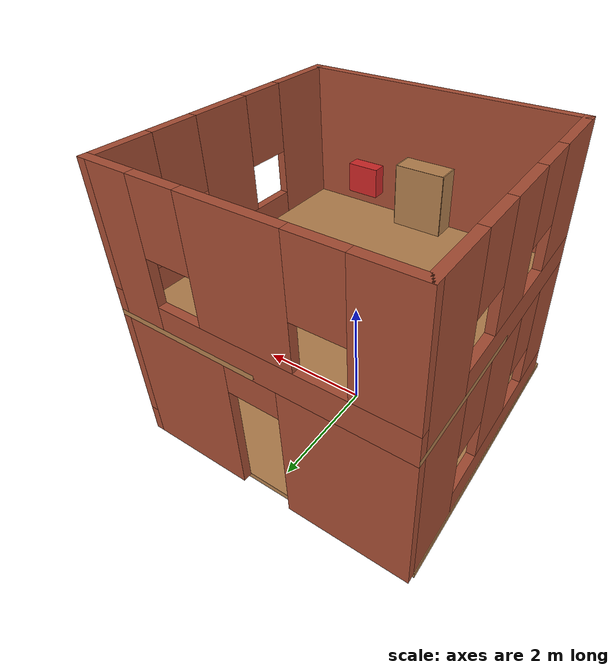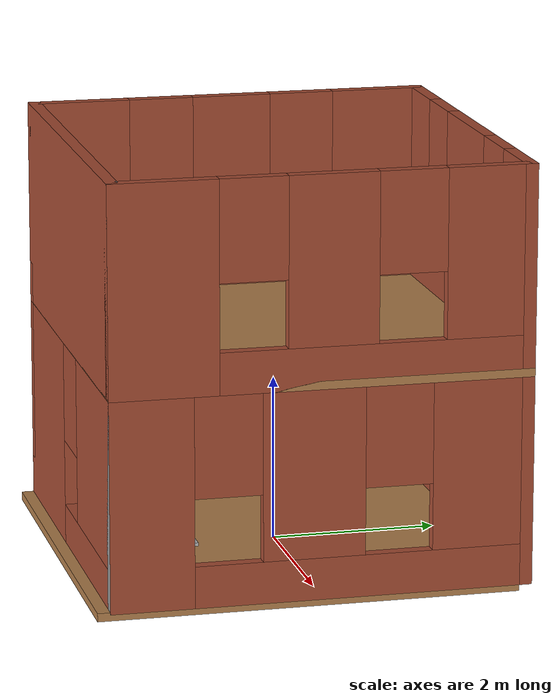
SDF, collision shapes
<?xml version='1.0'?>
<sdf version='1.6'>
  <model name='building1'>
    <link name='Floor_0'>
      <pose frame=''>0 0 2.5 0 -0 0</pose>
      <self_collide>0</self_collide>
      <enable_wind>0</enable_wind>
      <kinematic>0</kinematic>
      <gravity>1</gravity>
      <inertial>
        <mass>1</mass>
        <pose frame=''>0 0 0 0 -0 0</pose>
        <inertia>
          <ixx>1</ixx>
          <ixy>0</ixy>
          <ixz>0</ixz>
          <iyy>1</iyy>
          <iyz>0</iyz>
          <izz>1</izz>
        </inertia>
      </inertial>
      <visual name='Floor_0_Visual'>
        <pose frame=''>0 0 0.05 0 -0 0</pose>
        <geometry>
          <box>
            <size>5 5 0.1</size>
          </box>
        </geometry>
        <material>
          <script>
            <uri>file://media/materials/scripts/gazebo.material</uri>
            <name>Gazebo/Wood</name>
          </script>
          <ambient>1 1 1 1</ambient>
          <shader type='pixel'>
            <normal_map>__default__</normal_map>
          </shader>
        </material>
        <meta>
          <layer>1</layer>
        </meta>
        <transparency>0</transparency>
        <cast_shadows>1</cast_shadows>
      </visual>
      <collision name='Floor_0_Collision'>
        <laser_retro>0</laser_retro>
        <max_contacts>10</max_contacts>
        <pose frame=''>0 0 0.05 0 -0 0</pose>
        <geometry>
          <box>
            <size>5 5 0.1</size>
          </box>
        </geometry>
        <surface>
          <friction>
            <ode>
              <mu>1</mu>
              <mu2>1</mu2>
              <fdir1>0 0 0</fdir1>
              <slip1>0</slip1>
              <slip2>0</slip2>
            </ode>
            <torsional>
              <coefficient>1</coefficient>
              <patch_radius>0</patch_radius>
              <surface_radius>0</surface_radius>
              <use_patch_radius>1</use_patch_radius>
              <ode>
                <slip>0</slip>
              </ode>
            </torsional>
          </friction>
          <bounce>
            <restitution_coefficient>0</restitution_coefficient>
            <threshold>1e+06</threshold>
          </bounce>
          <contact>
            <collide_without_contact>0</collide_without_contact>
            <collide_without_contact_bitmask>1</collide_without_contact_bitmask>
            <collide_bitmask>1</collide_bitmask>
            <ode>
              <soft_cfm>0</soft_cfm>
              <soft_erp>0.2</soft_erp>
              <kp>1e+13</kp>
              <kd>1</kd>
              <max_vel>0.01</max_vel>
              <min_depth>0</min_depth>
            </ode>
            <bullet>
              <split_impulse>1</split_impulse>
              <split_impulse_penetration_threshold>-0.01</split_impulse_penetration_threshold>
              <soft_cfm>0</soft_cfm>
              <soft_erp>0.2</soft_erp>
              <kp>1e+13</kp>
              <kd>1</kd>
            </bullet>
          </contact>
        </surface>
      </collision>
    </link>
    <link name='Floor_0_clone'>
      <pose frame=''>-0.013101 -0.148574 -0.075535 0 -0 0</pose>
      <self_collide>0</self_collide>
      <enable_wind>0</enable_wind>
      <kinematic>0</kinematic>
      <gravity>0</gravity>
      <inertial>
        <mass>1</mass>
        <pose frame=''>0 0 0 0 -0 0</pose>
        <inertia>
          <ixx>1</ixx>
          <ixy>0</ixy>
          <ixz>0</ixz>
          <iyy>1</iyy>
          <iyz>0</iyz>
          <izz>1</izz>
        </inertia>
      </inertial>
      <visual name='Floor_0_Visual'>
        <pose frame=''>0 0 0.05 0 -0 0</pose>
        <geometry>
          <box>
            <size>5 5 0.1</size>
          </box>
        </geometry>
        <material>
          <script>
            <uri>file://media/materials/scripts/gazebo.material</uri>
            <name>Gazebo/Wood</name>
          </script>
          <ambient>1 1 1 1</ambient>
          <shader type='pixel'>
            <normal_map>__default__</normal_map>
          </shader>
        </material>
        <meta>
          <layer>1</layer>
        </meta>
        <transparency>0</transparency>
        <cast_shadows>1</cast_shadows>
      </visual>
      <collision name='Floor_0_Collision'>
        <laser_retro>0</laser_retro>
        <max_contacts>10</max_contacts>
        <pose frame=''>0 0 0.05 0 -0 0</pose>
        <geometry>
          <box>
            <size>5 5 0.1</size>
          </box>
        </geometry>
        <surface>
          <friction>
            <ode>
              <mu>1</mu>
              <mu2>1</mu2>
              <fdir1>0 0 0</fdir1>
              <slip1>0</slip1>
              <slip2>0</slip2>
            </ode>
            <torsional>
              <coefficient>1</coefficient>
              <patch_radius>0</patch_radius>
              <surface_radius>0</surface_radius>
              <use_patch_radius>1</use_patch_radius>
              <ode>
                <slip>0</slip>
              </ode>
            </torsional>
          </friction>
          <bounce>
            <restitution_coefficient>0</restitution_coefficient>
            <threshold>1e+06</threshold>
          </bounce>
          <contact>
            <collide_without_contact>0</collide_without_contact>
            <collide_without_contact_bitmask>1</collide_without_contact_bitmask>
            <collide_bitmask>1</collide_bitmask>
            <ode>
              <soft_cfm>0</soft_cfm>
              <soft_erp>0.2</soft_erp>
              <kp>1e+13</kp>
              <kd>1</kd>
              <max_vel>0.01</max_vel>
              <min_depth>0</min_depth>
            </ode>
            <bullet>
              <split_impulse>1</split_impulse>
              <split_impulse_penetration_threshold>-0.01</split_impulse_penetration_threshold>
              <soft_cfm>0</soft_cfm>
              <soft_erp>0.2</soft_erp>
              <kp>1e+13</kp>
              <kd>1</kd>
            </bullet>
          </contact>
        </surface>
      </collision>
    </link>
    <link name='Wall_1'>
      <pose frame=''>0 -2.425 0 0 -0 0</pose>
      <self_collide>0</self_collide>
      <enable_wind>0</enable_wind>
      <kinematic>0</kinematic>
      <visual name='Wall_1_Visual_3'>
        <pose frame=''>0.109106 0 1.9 0 -0 0</pose>
        <geometry>
          <box>
            <size>0.8 0.15 1.2</size>
          </box>
        </geometry>
        <material>
          <script>
            <uri>file://media/materials/scripts/gazebo.material</uri>
            <name>Gazebo/Bricks</name>
          </script>
          <ambient>1 1 1 1</ambient>
          <shader type='pixel'/>
        </material>
        <meta>
          <layer>0</layer>
        </meta>
        <transparency>0</transparency>
        <cast_shadows>1</cast_shadows>
      </visual>
      <visual name='Wall_1_Visual_1'>
        <pose frame=''>1.10455 0 0.25 0 -0 0</pose>
        <geometry>
          <box>
            <size>2.79089 0.15 0.5</size>
          </box>
        </geometry>
        <material>
          <script>
            <uri>file://media/materials/scripts/gazebo.material</uri>
            <name>Gazebo/Bricks</name>
          </script>
          <ambient>1 1 1 1</ambient>
          <shader type='pixel'/>
        </material>
        <meta>
          <layer>0</layer>
        </meta>
        <transparency>0</transparency>
        <cast_shadows>1</cast_shadows>
      </visual>
      <visual name='Wall_1_Visual_2'>
        <pose frame=''>1.50455 0 1.5 0 -0 0</pose>
        <geometry>
          <box>
            <size>1.99089 0.15 2</size>
          </box>
        </geometry>
        <material>
          <script>
            <uri>file://media/materials/scripts/gazebo.material</uri>
            <name>Gazebo/Bricks</name>
          </script>
          <ambient>1 1 1 1</ambient>
          <shader type='pixel'/>
        </material>
        <meta>
          <layer>0</layer>
        </meta>
        <transparency>0</transparency>
        <cast_shadows>1</cast_shadows>
      </visual>
      <visual name='Wall_1_Visual_0'>
        <pose frame=''>-1.39545 0 1.25 0 -0 0</pose>
        <geometry>
          <box>
            <size>2.20911 0.15 2.5</size>
          </box>
        </geometry>
        <material>
          <script>
            <uri>file://media/materials/scripts/gazebo.material</uri>
            <name>Gazebo/Bricks</name>
          </script>
          <ambient>1 1 1 1</ambient>
          <shader type='pixel'/>
        </material>
        <meta>
          <layer>0</layer>
        </meta>
        <transparency>0</transparency>
        <cast_shadows>1</cast_shadows>
      </visual>
      <collision name='Wall_1_Collision_3'>
        <laser_retro>0</laser_retro>
        <max_contacts>10</max_contacts>
        <pose frame=''>0.109106 0 1.9 0 -0 0</pose>
        <geometry>
          <box>
            <size>0.8 0.15 1.2</size>
          </box>
        </geometry>
        <surface>
          <friction>
            <ode>
              <mu>1</mu>
              <mu2>1</mu2>
              <fdir1>0 0 0</fdir1>
              <slip1>0</slip1>
              <slip2>0</slip2>
            </ode>
            <torsional>
              <coefficient>1</coefficient>
              <patch_radius>0</patch_radius>
              <surface_radius>0</surface_radius>
              <use_patch_radius>1</use_patch_radius>
              <ode>
                <slip>0</slip>
              </ode>
            </torsional>
          </friction>
          <bounce>
            <restitution_coefficient>0</restitution_coefficient>
            <threshold>1e+06</threshold>
          </bounce>
          <contact>
            <collide_without_contact>0</collide_without_contact>
            <collide_without_contact_bitmask>1</collide_without_contact_bitmask>
            <collide_bitmask>1</collide_bitmask>
            <ode>
              <soft_cfm>0</soft_cfm>
              <soft_erp>0.2</soft_erp>
              <kp>1e+13</kp>
              <kd>1</kd>
              <max_vel>0.01</max_vel>
              <min_depth>0</min_depth>
            </ode>
            <bullet>
              <split_impulse>1</split_impulse>
              <split_impulse_penetration_threshold>-0.01</split_impulse_penetration_threshold>
              <soft_cfm>0</soft_cfm>
              <soft_erp>0.2</soft_erp>
              <kp>1e+13</kp>
              <kd>1</kd>
            </bullet>
          </contact>
        </surface>
      </collision>
      <collision name='Wall_1_Collision_2'>
        <laser_retro>0</laser_retro>
        <max_contacts>10</max_contacts>
        <pose frame=''>1.50455 0 1.5 0 -0 0</pose>
        <geometry>
          <box>
            <size>1.99089 0.15 2</size>
          </box>
        </geometry>
        <surface>
          <friction>
            <ode>
              <mu>1</mu>
              <mu2>1</mu2>
              <fdir1>0 0 0</fdir1>
              <slip1>0</slip1>
              <slip2>0</slip2>
            </ode>
            <torsional>
              <coefficient>1</coefficient>
              <patch_radius>0</patch_radius>
              <surface_radius>0</surface_radius>
              <use_patch_radius>1</use_patch_radius>
              <ode>
                <slip>0</slip>
              </ode>
            </torsional>
          </friction>
          <bounce>
            <restitution_coefficient>0</restitution_coefficient>
            <threshold>1e+06</threshold>
          </bounce>
          <contact>
            <collide_without_contact>0</collide_without_contact>
            <collide_without_contact_bitmask>1</collide_without_contact_bitmask>
            <collide_bitmask>1</collide_bitmask>
            <ode>
              <soft_cfm>0</soft_cfm>
              <soft_erp>0.2</soft_erp>
              <kp>1e+13</kp>
              <kd>1</kd>
              <max_vel>0.01</max_vel>
              <min_depth>0</min_depth>
            </ode>
            <bullet>
              <split_impulse>1</split_impulse>
              <split_impulse_penetration_threshold>-0.01</split_impulse_penetration_threshold>
              <soft_cfm>0</soft_cfm>
              <soft_erp>0.2</soft_erp>
              <kp>1e+13</kp>
              <kd>1</kd>
            </bullet>
          </contact>
        </surface>
      </collision>
      <collision name='Wall_1_Collision_1'>
        <laser_retro>0</laser_retro>
        <max_contacts>10</max_contacts>
        <pose frame=''>1.10455 0 0.25 0 -0 0</pose>
        <geometry>
          <box>
            <size>2.79089 0.15 0.5</size>
          </box>
        </geometry>
        <surface>
          <friction>
            <ode>
              <mu>1</mu>
              <mu2>1</mu2>
              <fdir1>0 0 0</fdir1>
              <slip1>0</slip1>
              <slip2>0</slip2>
            </ode>
            <torsional>
              <coefficient>1</coefficient>
              <patch_radius>0</patch_radius>
              <surface_radius>0</surface_radius>
              <use_patch_radius>1</use_patch_radius>
              <ode>
                <slip>0</slip>
              </ode>
            </torsional>
          </friction>
          <bounce>
            <restitution_coefficient>0</restitution_coefficient>
            <threshold>1e+06</threshold>
          </bounce>
          <contact>
            <collide_without_contact>0</collide_without_contact>
            <collide_without_contact_bitmask>1</collide_without_contact_bitmask>
            <collide_bitmask>1</collide_bitmask>
            <ode>
              <soft_cfm>0</soft_cfm>
              <soft_erp>0.2</soft_erp>
              <kp>1e+13</kp>
              <kd>1</kd>
              <max_vel>0.01</max_vel>
              <min_depth>0</min_depth>
            </ode>
            <bullet>
              <split_impulse>1</split_impulse>
              <split_impulse_penetration_threshold>-0.01</split_impulse_penetration_threshold>
              <soft_cfm>0</soft_cfm>
              <soft_erp>0.2</soft_erp>
              <kp>1e+13</kp>
              <kd>1</kd>
            </bullet>
          </contact>
        </surface>
      </collision>
      <collision name='Wall_1_Collision_0'>
        <laser_retro>0</laser_retro>
        <max_contacts>10</max_contacts>
        <pose frame=''>-1.39545 0 1.25 0 -0 0</pose>
        <geometry>
          <box>
            <size>2.20911 0.15 2.5</size>
          </box>
        </geometry>
        <surface>
          <friction>
            <ode>
              <mu>1</mu>
              <mu2>1</mu2>
              <fdir1>0 0 0</fdir1>
              <slip1>0</slip1>
              <slip2>0</slip2>
            </ode>
            <torsional>
              <coefficient>1</coefficient>
              <patch_radius>0</patch_radius>
              <surface_radius>0</surface_radius>
              <use_patch_radius>1</use_patch_radius>
              <ode>
                <slip>0</slip>
              </ode>
            </torsional>
          </friction>
          <bounce>
            <restitution_coefficient>0</restitution_coefficient>
            <threshold>1e+06</threshold>
          </bounce>
          <contact>
            <collide_without_contact>0</collide_without_contact>
            <collide_without_contact_bitmask>1</collide_without_contact_bitmask>
            <collide_bitmask>1</collide_bitmask>
            <ode>
              <soft_cfm>0</soft_cfm>
              <soft_erp>0.2</soft_erp>
              <kp>1e+13</kp>
              <kd>1</kd>
              <max_vel>0.01</max_vel>
              <min_depth>0</min_depth>
            </ode>
            <bullet>
              <split_impulse>1</split_impulse>
              <split_impulse_penetration_threshold>-0.01</split_impulse_penetration_threshold>
              <soft_cfm>0</soft_cfm>
              <soft_erp>0.2</soft_erp>
              <kp>1e+13</kp>
              <kd>1</kd>
            </bullet>
          </contact>
        </surface>
      </collision>
    </link>
    <link name='Wall_10'>
      <pose frame=''>0 2.425 2.5 0 -0 3.14159</pose>
      <self_collide>0</self_collide>
      <enable_wind>0</enable_wind>
      <kinematic>0</kinematic>
      <visual name='Wall_10_Visual_1'>
        <pose frame=''>0.447808 0 0.25 0 -0 0</pose>
        <geometry>
          <box>
            <size>4.10438 0.15 0.5</size>
          </box>
        </geometry>
        <material>
          <script>
            <uri>file://media/materials/scripts/gazebo.material</uri>
            <name>Gazebo/Bricks</name>
          </script>
          <ambient>1 1 1 1</ambient>
          <shader type='pixel'/>
        </material>
        <meta>
          <layer>1</layer>
        </meta>
        <transparency>0</transparency>
        <cast_shadows>1</cast_shadows>
      </visual>
      <visual name='Wall_10_Visual_5'>
        <pose frame=''>1.14562 0 1.9 0 -0 0</pose>
        <geometry>
          <box>
            <size>0.8 0.15 1.2</size>
          </box>
        </geometry>
        <material>
          <script>
            <uri>file://media/materials/scripts/gazebo.material</uri>
            <name>Gazebo/Bricks</name>
          </script>
          <ambient>1 1 1 1</ambient>
          <shader type='pixel'/>
        </material>
        <meta>
          <layer>1</layer>
        </meta>
        <transparency>0</transparency>
        <cast_shadows>1</cast_shadows>
      </visual>
      <visual name='Wall_10_Visual_0'>
        <pose frame=''>-2.05219 0 1.25 0 -0 0</pose>
        <geometry>
          <box>
            <size>0.895617 0.15 2.5</size>
          </box>
        </geometry>
        <material>
          <script>
            <uri>file://media/materials/scripts/gazebo.material</uri>
            <name>Gazebo/Bricks</name>
          </script>
          <ambient>1 1 1 1</ambient>
          <shader type='pixel'/>
        </material>
        <meta>
          <layer>1</layer>
        </meta>
        <transparency>0</transparency>
        <cast_shadows>1</cast_shadows>
      </visual>
      <visual name='Wall_10_Visual_3'>
        <pose frame=''>2.02281 0 1.5 0 -0 0</pose>
        <geometry>
          <box>
            <size>0.954383 0.15 2</size>
          </box>
        </geometry>
        <material>
          <script>
            <uri>file://media/materials/scripts/gazebo.material</uri>
            <name>Gazebo/Bricks</name>
          </script>
          <ambient>1 1 1 1</ambient>
          <shader type='pixel'/>
        </material>
        <meta>
          <layer>1</layer>
        </meta>
        <transparency>0</transparency>
        <cast_shadows>1</cast_shadows>
      </visual>
      <visual name='Wall_10_Visual_2'>
        <pose frame=''>-0.029383 0 1.5 0 -0 0</pose>
        <geometry>
          <box>
            <size>1.55 0.15 2</size>
          </box>
        </geometry>
        <material>
          <script>
            <uri>file://media/materials/scripts/gazebo.material</uri>
            <name>Gazebo/Bricks</name>
          </script>
          <ambient>1 1 1 1</ambient>
          <shader type='pixel'/>
        </material>
        <meta>
          <layer>1</layer>
        </meta>
        <transparency>0</transparency>
        <cast_shadows>1</cast_shadows>
      </visual>
      <visual name='Wall_10_Visual_4'>
        <pose frame=''>-1.20438 0 1.9 0 -0 0</pose>
        <geometry>
          <box>
            <size>0.8 0.15 1.2</size>
          </box>
        </geometry>
        <material>
          <script>
            <uri>file://media/materials/scripts/gazebo.material</uri>
            <name>Gazebo/Bricks</name>
          </script>
          <ambient>1 1 1 1</ambient>
          <shader type='pixel'/>
        </material>
        <meta>
          <layer>1</layer>
        </meta>
        <transparency>0</transparency>
        <cast_shadows>1</cast_shadows>
      </visual>
      <collision name='Wall_10_Collision_2'>
        <laser_retro>0</laser_retro>
        <max_contacts>10</max_contacts>
        <pose frame=''>-0.029383 0 1.5 0 -0 0</pose>
        <geometry>
          <box>
            <size>1.55 0.15 2</size>
          </box>
        </geometry>
        <surface>
          <friction>
            <ode>
              <mu>1</mu>
              <mu2>1</mu2>
              <fdir1>0 0 0</fdir1>
              <slip1>0</slip1>
              <slip2>0</slip2>
            </ode>
            <torsional>
              <coefficient>1</coefficient>
              <patch_radius>0</patch_radius>
              <surface_radius>0</surface_radius>
              <use_patch_radius>1</use_patch_radius>
              <ode>
                <slip>0</slip>
              </ode>
            </torsional>
          </friction>
          <bounce>
            <restitution_coefficient>0</restitution_coefficient>
            <threshold>1e+06</threshold>
          </bounce>
          <contact>
            <collide_without_contact>0</collide_without_contact>
            <collide_without_contact_bitmask>1</collide_without_contact_bitmask>
            <collide_bitmask>1</collide_bitmask>
            <ode>
              <soft_cfm>0</soft_cfm>
              <soft_erp>0.2</soft_erp>
              <kp>1e+13</kp>
              <kd>1</kd>
              <max_vel>0.01</max_vel>
              <min_depth>0</min_depth>
            </ode>
            <bullet>
              <split_impulse>1</split_impulse>
              <split_impulse_penetration_threshold>-0.01</split_impulse_penetration_threshold>
              <soft_cfm>0</soft_cfm>
              <soft_erp>0.2</soft_erp>
              <kp>1e+13</kp>
              <kd>1</kd>
            </bullet>
          </contact>
        </surface>
      </collision>
      <collision name='Wall_10_Collision_1'>
        <laser_retro>0</laser_retro>
        <max_contacts>10</max_contacts>
        <pose frame=''>0.447808 0 0.25 0 -0 0</pose>
        <geometry>
          <box>
            <size>4.10438 0.15 0.5</size>
          </box>
        </geometry>
        <surface>
          <friction>
            <ode>
              <mu>1</mu>
              <mu2>1</mu2>
              <fdir1>0 0 0</fdir1>
              <slip1>0</slip1>
              <slip2>0</slip2>
            </ode>
            <torsional>
              <coefficient>1</coefficient>
              <patch_radius>0</patch_radius>
              <surface_radius>0</surface_radius>
              <use_patch_radius>1</use_patch_radius>
              <ode>
                <slip>0</slip>
              </ode>
            </torsional>
          </friction>
          <bounce>
            <restitution_coefficient>0</restitution_coefficient>
            <threshold>1e+06</threshold>
          </bounce>
          <contact>
            <collide_without_contact>0</collide_without_contact>
            <collide_without_contact_bitmask>1</collide_without_contact_bitmask>
            <collide_bitmask>1</collide_bitmask>
            <ode>
              <soft_cfm>0</soft_cfm>
              <soft_erp>0.2</soft_erp>
              <kp>1e+13</kp>
              <kd>1</kd>
              <max_vel>0.01</max_vel>
              <min_depth>0</min_depth>
            </ode>
            <bullet>
              <split_impulse>1</split_impulse>
              <split_impulse_penetration_threshold>-0.01</split_impulse_penetration_threshold>
              <soft_cfm>0</soft_cfm>
              <soft_erp>0.2</soft_erp>
              <kp>1e+13</kp>
              <kd>1</kd>
            </bullet>
          </contact>
        </surface>
      </collision>
      <collision name='Wall_10_Collision_5'>
        <laser_retro>0</laser_retro>
        <max_contacts>10</max_contacts>
        <pose frame=''>1.14562 0 1.9 0 -0 0</pose>
        <geometry>
          <box>
            <size>0.8 0.15 1.2</size>
          </box>
        </geometry>
        <surface>
          <friction>
            <ode>
              <mu>1</mu>
              <mu2>1</mu2>
              <fdir1>0 0 0</fdir1>
              <slip1>0</slip1>
              <slip2>0</slip2>
            </ode>
            <torsional>
              <coefficient>1</coefficient>
              <patch_radius>0</patch_radius>
              <surface_radius>0</surface_radius>
              <use_patch_radius>1</use_patch_radius>
              <ode>
                <slip>0</slip>
              </ode>
            </torsional>
          </friction>
          <bounce>
            <restitution_coefficient>0</restitution_coefficient>
            <threshold>1e+06</threshold>
          </bounce>
          <contact>
            <collide_without_contact>0</collide_without_contact>
            <collide_without_contact_bitmask>1</collide_without_contact_bitmask>
            <collide_bitmask>1</collide_bitmask>
            <ode>
              <soft_cfm>0</soft_cfm>
              <soft_erp>0.2</soft_erp>
              <kp>1e+13</kp>
              <kd>1</kd>
              <max_vel>0.01</max_vel>
              <min_depth>0</min_depth>
            </ode>
            <bullet>
              <split_impulse>1</split_impulse>
              <split_impulse_penetration_threshold>-0.01</split_impulse_penetration_threshold>
              <soft_cfm>0</soft_cfm>
              <soft_erp>0.2</soft_erp>
              <kp>1e+13</kp>
              <kd>1</kd>
            </bullet>
          </contact>
        </surface>
      </collision>
      <collision name='Wall_10_Collision_0'>
        <laser_retro>0</laser_retro>
        <max_contacts>10</max_contacts>
        <pose frame=''>-2.05219 0 1.25 0 -0 0</pose>
        <geometry>
          <box>
            <size>0.895617 0.15 2.5</size>
          </box>
        </geometry>
        <surface>
          <friction>
            <ode>
              <mu>1</mu>
              <mu2>1</mu2>
              <fdir1>0 0 0</fdir1>
              <slip1>0</slip1>
              <slip2>0</slip2>
            </ode>
            <torsional>
              <coefficient>1</coefficient>
              <patch_radius>0</patch_radius>
              <surface_radius>0</surface_radius>
              <use_patch_radius>1</use_patch_radius>
              <ode>
                <slip>0</slip>
              </ode>
            </torsional>
          </friction>
          <bounce>
            <restitution_coefficient>0</restitution_coefficient>
            <threshold>1e+06</threshold>
          </bounce>
          <contact>
            <collide_without_contact>0</collide_without_contact>
            <collide_without_contact_bitmask>1</collide_without_contact_bitmask>
            <collide_bitmask>1</collide_bitmask>
            <ode>
              <soft_cfm>0</soft_cfm>
              <soft_erp>0.2</soft_erp>
              <kp>1e+13</kp>
              <kd>1</kd>
              <max_vel>0.01</max_vel>
              <min_depth>0</min_depth>
            </ode>
            <bullet>
              <split_impulse>1</split_impulse>
              <split_impulse_penetration_threshold>-0.01</split_impulse_penetration_threshold>
              <soft_cfm>0</soft_cfm>
              <soft_erp>0.2</soft_erp>
              <kp>1e+13</kp>
              <kd>1</kd>
            </bullet>
          </contact>
        </surface>
      </collision>
      <collision name='Wall_10_Collision_4'>
        <laser_retro>0</laser_retro>
        <max_contacts>10</max_contacts>
        <pose frame=''>-1.20438 0 1.9 0 -0 0</pose>
        <geometry>
          <box>
            <size>0.8 0.15 1.2</size>
          </box>
        </geometry>
        <surface>
          <friction>
            <ode>
              <mu>1</mu>
              <mu2>1</mu2>
              <fdir1>0 0 0</fdir1>
              <slip1>0</slip1>
              <slip2>0</slip2>
            </ode>
            <torsional>
              <coefficient>1</coefficient>
              <patch_radius>0</patch_radius>
              <surface_radius>0</surface_radius>
              <use_patch_radius>1</use_patch_radius>
              <ode>
                <slip>0</slip>
              </ode>
            </torsional>
          </friction>
          <bounce>
            <restitution_coefficient>0</restitution_coefficient>
            <threshold>1e+06</threshold>
          </bounce>
          <contact>
            <collide_without_contact>0</collide_without_contact>
            <collide_without_contact_bitmask>1</collide_without_contact_bitmask>
            <collide_bitmask>1</collide_bitmask>
            <ode>
              <soft_cfm>0</soft_cfm>
              <soft_erp>0.2</soft_erp>
              <kp>1e+13</kp>
              <kd>1</kd>
              <max_vel>0.01</max_vel>
              <min_depth>0</min_depth>
            </ode>
            <bullet>
              <split_impulse>1</split_impulse>
              <split_impulse_penetration_threshold>-0.01</split_impulse_penetration_threshold>
              <soft_cfm>0</soft_cfm>
              <soft_erp>0.2</soft_erp>
              <kp>1e+13</kp>
              <kd>1</kd>
            </bullet>
          </contact>
        </surface>
      </collision>
      <collision name='Wall_10_Collision_3'>
        <laser_retro>0</laser_retro>
        <max_contacts>10</max_contacts>
        <pose frame=''>2.02281 0 1.5 0 -0 0</pose>
        <geometry>
          <box>
            <size>0.954383 0.15 2</size>
          </box>
        </geometry>
        <surface>
          <friction>
            <ode>
              <mu>1</mu>
              <mu2>1</mu2>
              <fdir1>0 0 0</fdir1>
              <slip1>0</slip1>
              <slip2>0</slip2>
            </ode>
            <torsional>
              <coefficient>1</coefficient>
              <patch_radius>0</patch_radius>
              <surface_radius>0</surface_radius>
              <use_patch_radius>1</use_patch_radius>
              <ode>
                <slip>0</slip>
              </ode>
            </torsional>
          </friction>
          <bounce>
            <restitution_coefficient>0</restitution_coefficient>
            <threshold>1e+06</threshold>
          </bounce>
          <contact>
            <collide_without_contact>0</collide_without_contact>
            <collide_without_contact_bitmask>1</collide_without_contact_bitmask>
            <collide_bitmask>1</collide_bitmask>
            <ode>
              <soft_cfm>0</soft_cfm>
              <soft_erp>0.2</soft_erp>
              <kp>1e+13</kp>
              <kd>1</kd>
              <max_vel>0.01</max_vel>
              <min_depth>0</min_depth>
            </ode>
            <bullet>
              <split_impulse>1</split_impulse>
              <split_impulse_penetration_threshold>-0.01</split_impulse_penetration_threshold>
              <soft_cfm>0</soft_cfm>
              <soft_erp>0.2</soft_erp>
              <kp>1e+13</kp>
              <kd>1</kd>
            </bullet>
          </contact>
        </surface>
      </collision>
    </link>
    <link name='Wall_11'>
      <pose frame=''>-2.425 0 2.5 0 0 -1.5708</pose>
      <self_collide>0</self_collide>
      <enable_wind>0</enable_wind>
      <kinematic>0</kinematic>
      <visual name='Wall_11_Visual_0'>
        <pose frame=''>-1.91127 0 1.25 0 -0 0</pose>
        <geometry>
          <box>
            <size>1.17746 0.15 2.5</size>
          </box>
        </geometry>
        <material>
          <script>
            <uri>file://media/materials/scripts/gazebo.material</uri>
            <name>Gazebo/Bricks</name>
          </script>
          <ambient>1 1 1 1</ambient>
          <shader type='pixel'/>
        </material>
        <meta>
          <layer>1</layer>
        </meta>
        <transparency>0</transparency>
        <cast_shadows>1</cast_shadows>
      </visual>
      <visual name='Wall_11_Visual_4'>
        <pose frame=''>-0.922536 0 1.9 0 -0 0</pose>
        <geometry>
          <box>
            <size>0.8 0.15 1.2</size>
          </box>
        </geometry>
        <material>
          <script>
            <uri>file://media/materials/scripts/gazebo.material</uri>
            <name>Gazebo/Bricks</name>
          </script>
          <ambient>1 1 1 1</ambient>
          <shader type='pixel'/>
        </material>
        <meta>
          <layer>1</layer>
        </meta>
        <transparency>0</transparency>
        <cast_shadows>1</cast_shadows>
      </visual>
      <visual name='Wall_11_Visual_1'>
        <pose frame=''>0.588732 0 0.25 0 -0 0</pose>
        <geometry>
          <box>
            <size>3.82254 0.15 0.5</size>
          </box>
        </geometry>
        <material>
          <script>
            <uri>file://media/materials/scripts/gazebo.material</uri>
            <name>Gazebo/Bricks</name>
          </script>
          <ambient>1 1 1 1</ambient>
          <shader type='pixel'/>
        </material>
        <meta>
          <layer>1</layer>
        </meta>
        <transparency>0</transparency>
        <cast_shadows>1</cast_shadows>
      </visual>
      <visual name='Wall_11_Visual_5'>
        <pose frame=''>0.857464 0 1.9 0 -0 0</pose>
        <geometry>
          <box>
            <size>0.8 0.15 1.2</size>
          </box>
        </geometry>
        <material>
          <script>
            <uri>file://media/materials/scripts/gazebo.material</uri>
            <name>Gazebo/Bricks</name>
          </script>
          <ambient>1 1 1 1</ambient>
          <shader type='pixel'/>
        </material>
        <meta>
          <layer>1</layer>
        </meta>
        <transparency>0</transparency>
        <cast_shadows>1</cast_shadows>
      </visual>
      <visual name='Wall_11_Visual_3'>
        <pose frame=''>1.87873 0 1.5 0 -0 0</pose>
        <geometry>
          <box>
            <size>1.24254 0.15 2</size>
          </box>
        </geometry>
        <material>
          <script>
            <uri>file://media/materials/scripts/gazebo.material</uri>
            <name>Gazebo/Bricks</name>
          </script>
          <ambient>1 1 1 1</ambient>
          <shader type='pixel'/>
        </material>
        <meta>
          <layer>1</layer>
        </meta>
        <transparency>0</transparency>
        <cast_shadows>1</cast_shadows>
      </visual>
      <visual name='Wall_11_Visual_2'>
        <pose frame=''>-0.032536 0 1.5 0 -0 0</pose>
        <geometry>
          <box>
            <size>0.98 0.15 2</size>
          </box>
        </geometry>
        <material>
          <script>
            <uri>file://media/materials/scripts/gazebo.material</uri>
            <name>Gazebo/Bricks</name>
          </script>
          <ambient>1 1 1 1</ambient>
          <shader type='pixel'/>
        </material>
        <meta>
          <layer>1</layer>
        </meta>
        <transparency>0</transparency>
        <cast_shadows>1</cast_shadows>
      </visual>
      <collision name='Wall_11_Collision_5'>
        <laser_retro>0</laser_retro>
        <max_contacts>10</max_contacts>
        <pose frame=''>0.857464 0 1.9 0 -0 0</pose>
        <geometry>
          <box>
            <size>0.8 0.15 1.2</size>
          </box>
        </geometry>
        <surface>
          <friction>
            <ode>
              <mu>1</mu>
              <mu2>1</mu2>
              <fdir1>0 0 0</fdir1>
              <slip1>0</slip1>
              <slip2>0</slip2>
            </ode>
            <torsional>
              <coefficient>1</coefficient>
              <patch_radius>0</patch_radius>
              <surface_radius>0</surface_radius>
              <use_patch_radius>1</use_patch_radius>
              <ode>
                <slip>0</slip>
              </ode>
            </torsional>
          </friction>
          <bounce>
            <restitution_coefficient>0</restitution_coefficient>
            <threshold>1e+06</threshold>
          </bounce>
          <contact>
            <collide_without_contact>0</collide_without_contact>
            <collide_without_contact_bitmask>1</collide_without_contact_bitmask>
            <collide_bitmask>1</collide_bitmask>
            <ode>
              <soft_cfm>0</soft_cfm>
              <soft_erp>0.2</soft_erp>
              <kp>1e+13</kp>
              <kd>1</kd>
              <max_vel>0.01</max_vel>
              <min_depth>0</min_depth>
            </ode>
            <bullet>
              <split_impulse>1</split_impulse>
              <split_impulse_penetration_threshold>-0.01</split_impulse_penetration_threshold>
              <soft_cfm>0</soft_cfm>
              <soft_erp>0.2</soft_erp>
              <kp>1e+13</kp>
              <kd>1</kd>
            </bullet>
          </contact>
        </surface>
      </collision>
      <collision name='Wall_11_Collision_4'>
        <laser_retro>0</laser_retro>
        <max_contacts>10</max_contacts>
        <pose frame=''>-0.922536 0 1.9 0 -0 0</pose>
        <geometry>
          <box>
            <size>0.8 0.15 1.2</size>
          </box>
        </geometry>
        <surface>
          <friction>
            <ode>
              <mu>1</mu>
              <mu2>1</mu2>
              <fdir1>0 0 0</fdir1>
              <slip1>0</slip1>
              <slip2>0</slip2>
            </ode>
            <torsional>
              <coefficient>1</coefficient>
              <patch_radius>0</patch_radius>
              <surface_radius>0</surface_radius>
              <use_patch_radius>1</use_patch_radius>
              <ode>
                <slip>0</slip>
              </ode>
            </torsional>
          </friction>
          <bounce>
            <restitution_coefficient>0</restitution_coefficient>
            <threshold>1e+06</threshold>
          </bounce>
          <contact>
            <collide_without_contact>0</collide_without_contact>
            <collide_without_contact_bitmask>1</collide_without_contact_bitmask>
            <collide_bitmask>1</collide_bitmask>
            <ode>
              <soft_cfm>0</soft_cfm>
              <soft_erp>0.2</soft_erp>
              <kp>1e+13</kp>
              <kd>1</kd>
              <max_vel>0.01</max_vel>
              <min_depth>0</min_depth>
            </ode>
            <bullet>
              <split_impulse>1</split_impulse>
              <split_impulse_penetration_threshold>-0.01</split_impulse_penetration_threshold>
              <soft_cfm>0</soft_cfm>
              <soft_erp>0.2</soft_erp>
              <kp>1e+13</kp>
              <kd>1</kd>
            </bullet>
          </contact>
        </surface>
      </collision>
      <collision name='Wall_11_Collision_2'>
        <laser_retro>0</laser_retro>
        <max_contacts>10</max_contacts>
        <pose frame=''>-0.032536 0 1.5 0 -0 0</pose>
        <geometry>
          <box>
            <size>0.98 0.15 2</size>
          </box>
        </geometry>
        <surface>
          <friction>
            <ode>
              <mu>1</mu>
              <mu2>1</mu2>
              <fdir1>0 0 0</fdir1>
              <slip1>0</slip1>
              <slip2>0</slip2>
            </ode>
            <torsional>
              <coefficient>1</coefficient>
              <patch_radius>0</patch_radius>
              <surface_radius>0</surface_radius>
              <use_patch_radius>1</use_patch_radius>
              <ode>
                <slip>0</slip>
              </ode>
            </torsional>
          </friction>
          <bounce>
            <restitution_coefficient>0</restitution_coefficient>
            <threshold>1e+06</threshold>
          </bounce>
          <contact>
            <collide_without_contact>0</collide_without_contact>
            <collide_without_contact_bitmask>1</collide_without_contact_bitmask>
            <collide_bitmask>1</collide_bitmask>
            <ode>
              <soft_cfm>0</soft_cfm>
              <soft_erp>0.2</soft_erp>
              <kp>1e+13</kp>
              <kd>1</kd>
              <max_vel>0.01</max_vel>
              <min_depth>0</min_depth>
            </ode>
            <bullet>
              <split_impulse>1</split_impulse>
              <split_impulse_penetration_threshold>-0.01</split_impulse_penetration_threshold>
              <soft_cfm>0</soft_cfm>
              <soft_erp>0.2</soft_erp>
              <kp>1e+13</kp>
              <kd>1</kd>
            </bullet>
          </contact>
        </surface>
      </collision>
      <collision name='Wall_11_Collision_3'>
        <laser_retro>0</laser_retro>
        <max_contacts>10</max_contacts>
        <pose frame=''>1.87873 0 1.5 0 -0 0</pose>
        <geometry>
          <box>
            <size>1.24254 0.15 2</size>
          </box>
        </geometry>
        <surface>
          <friction>
            <ode>
              <mu>1</mu>
              <mu2>1</mu2>
              <fdir1>0 0 0</fdir1>
              <slip1>0</slip1>
              <slip2>0</slip2>
            </ode>
            <torsional>
              <coefficient>1</coefficient>
              <patch_radius>0</patch_radius>
              <surface_radius>0</surface_radius>
              <use_patch_radius>1</use_patch_radius>
              <ode>
                <slip>0</slip>
              </ode>
            </torsional>
          </friction>
          <bounce>
            <restitution_coefficient>0</restitution_coefficient>
            <threshold>1e+06</threshold>
          </bounce>
          <contact>
            <collide_without_contact>0</collide_without_contact>
            <collide_without_contact_bitmask>1</collide_without_contact_bitmask>
            <collide_bitmask>1</collide_bitmask>
            <ode>
              <soft_cfm>0</soft_cfm>
              <soft_erp>0.2</soft_erp>
              <kp>1e+13</kp>
              <kd>1</kd>
              <max_vel>0.01</max_vel>
              <min_depth>0</min_depth>
            </ode>
            <bullet>
              <split_impulse>1</split_impulse>
              <split_impulse_penetration_threshold>-0.01</split_impulse_penetration_threshold>
              <soft_cfm>0</soft_cfm>
              <soft_erp>0.2</soft_erp>
              <kp>1e+13</kp>
              <kd>1</kd>
            </bullet>
          </contact>
        </surface>
      </collision>
      <collision name='Wall_11_Collision_0'>
        <laser_retro>0</laser_retro>
        <max_contacts>10</max_contacts>
        <pose frame=''>-1.91127 0 1.25 0 -0 0</pose>
        <geometry>
          <box>
            <size>1.17746 0.15 2.5</size>
          </box>
        </geometry>
        <surface>
          <friction>
            <ode>
              <mu>1</mu>
              <mu2>1</mu2>
              <fdir1>0 0 0</fdir1>
              <slip1>0</slip1>
              <slip2>0</slip2>
            </ode>
            <torsional>
              <coefficient>1</coefficient>
              <patch_radius>0</patch_radius>
              <surface_radius>0</surface_radius>
              <use_patch_radius>1</use_patch_radius>
              <ode>
                <slip>0</slip>
              </ode>
            </torsional>
          </friction>
          <bounce>
            <restitution_coefficient>0</restitution_coefficient>
            <threshold>1e+06</threshold>
          </bounce>
          <contact>
            <collide_without_contact>0</collide_without_contact>
            <collide_without_contact_bitmask>1</collide_without_contact_bitmask>
            <collide_bitmask>1</collide_bitmask>
            <ode>
              <soft_cfm>0</soft_cfm>
              <soft_erp>0.2</soft_erp>
              <kp>1e+13</kp>
              <kd>1</kd>
              <max_vel>0.01</max_vel>
              <min_depth>0</min_depth>
            </ode>
            <bullet>
              <split_impulse>1</split_impulse>
              <split_impulse_penetration_threshold>-0.01</split_impulse_penetration_threshold>
              <soft_cfm>0</soft_cfm>
              <soft_erp>0.2</soft_erp>
              <kp>1e+13</kp>
              <kd>1</kd>
            </bullet>
          </contact>
        </surface>
      </collision>
      <collision name='Wall_11_Collision_1'>
        <laser_retro>0</laser_retro>
        <max_contacts>10</max_contacts>
        <pose frame=''>0.588732 0 0.25 0 -0 0</pose>
        <geometry>
          <box>
            <size>3.82254 0.15 0.5</size>
          </box>
        </geometry>
        <surface>
          <friction>
            <ode>
              <mu>1</mu>
              <mu2>1</mu2>
              <fdir1>0 0 0</fdir1>
              <slip1>0</slip1>
              <slip2>0</slip2>
            </ode>
            <torsional>
              <coefficient>1</coefficient>
              <patch_radius>0</patch_radius>
              <surface_radius>0</surface_radius>
              <use_patch_radius>1</use_patch_radius>
              <ode>
                <slip>0</slip>
              </ode>
            </torsional>
          </friction>
          <bounce>
            <restitution_coefficient>0</restitution_coefficient>
            <threshold>1e+06</threshold>
          </bounce>
          <contact>
            <collide_without_contact>0</collide_without_contact>
            <collide_without_contact_bitmask>1</collide_without_contact_bitmask>
            <collide_bitmask>1</collide_bitmask>
            <ode>
              <soft_cfm>0</soft_cfm>
              <soft_erp>0.2</soft_erp>
              <kp>1e+13</kp>
              <kd>1</kd>
              <max_vel>0.01</max_vel>
              <min_depth>0</min_depth>
            </ode>
            <bullet>
              <split_impulse>1</split_impulse>
              <split_impulse_penetration_threshold>-0.01</split_impulse_penetration_threshold>
              <soft_cfm>0</soft_cfm>
              <soft_erp>0.2</soft_erp>
              <kp>1e+13</kp>
              <kd>1</kd>
            </bullet>
          </contact>
        </surface>
      </collision>
    </link>
    <link name='Wall_2'>
      <pose frame=''>2.425 -2.425 0 0 -0 0</pose>
      <self_collide>0</self_collide>
      <enable_wind>0</enable_wind>
      <kinematic>0</kinematic>
      <visual name='Wall_2_Visual'>
        <pose frame=''>0 0 1.25 0 -0 0</pose>
        <geometry>
          <box>
            <size>0.15 0.15 2.5</size>
          </box>
        </geometry>
        <material>
          <script>
            <uri>file://media/materials/scripts/gazebo.material</uri>
            <name>Gazebo/Grey</name>
          </script>
          <ambient>1 1 1 1</ambient>
          <shader type='pixel'/>
        </material>
        <meta>
          <layer>0</layer>
        </meta>
        <transparency>0</transparency>
        <cast_shadows>1</cast_shadows>
      </visual>
      <collision name='Wall_2_Collision'>
        <laser_retro>0</laser_retro>
        <max_contacts>10</max_contacts>
        <pose frame=''>0 0 1.25 0 -0 0</pose>
        <geometry>
          <box>
            <size>0.15 0.15 2.5</size>
          </box>
        </geometry>
        <surface>
          <friction>
            <ode>
              <mu>1</mu>
              <mu2>1</mu2>
              <fdir1>0 0 0</fdir1>
              <slip1>0</slip1>
              <slip2>0</slip2>
            </ode>
            <torsional>
              <coefficient>1</coefficient>
              <patch_radius>0</patch_radius>
              <surface_radius>0</surface_radius>
              <use_patch_radius>1</use_patch_radius>
              <ode>
                <slip>0</slip>
              </ode>
            </torsional>
          </friction>
          <bounce>
            <restitution_coefficient>0</restitution_coefficient>
            <threshold>1e+06</threshold>
          </bounce>
          <contact>
            <collide_without_contact>0</collide_without_contact>
            <collide_without_contact_bitmask>1</collide_without_contact_bitmask>
            <collide_bitmask>1</collide_bitmask>
            <ode>
              <soft_cfm>0</soft_cfm>
              <soft_erp>0.2</soft_erp>
              <kp>1e+13</kp>
              <kd>1</kd>
              <max_vel>0.01</max_vel>
              <min_depth>0</min_depth>
            </ode>
            <bullet>
              <split_impulse>1</split_impulse>
              <split_impulse_penetration_threshold>-0.01</split_impulse_penetration_threshold>
              <soft_cfm>0</soft_cfm>
              <soft_erp>0.2</soft_erp>
              <kp>1e+13</kp>
              <kd>1</kd>
            </bullet>
          </contact>
        </surface>
      </collision>
    </link>
    <link name='Wall_3'>
      <pose frame=''>2.425 0 0 0 -0 1.5708</pose>
      <self_collide>0</self_collide>
      <enable_wind>0</enable_wind>
      <kinematic>0</kinematic>
      <visual name='Wall_3_Visual_4'>
        <pose frame=''>-1.11345 0 1.9 0 -0 0</pose>
        <geometry>
          <box>
            <size>0.8 0.15 1.2</size>
          </box>
        </geometry>
        <material>
          <script>
            <uri>file://media/materials/scripts/gazebo.material</uri>
            <name>Gazebo/Bricks</name>
          </script>
          <ambient>1 1 1 1</ambient>
          <shader type='pixel'/>
        </material>
        <meta>
          <layer>0</layer>
        </meta>
        <transparency>0</transparency>
        <cast_shadows>1</cast_shadows>
      </visual>
      <visual name='Wall_3_Visual_2'>
        <pose frame=''>-0.109669 0 1.5 0 -0 0</pose>
        <geometry>
          <box>
            <size>1.20755 0.15 2</size>
          </box>
        </geometry>
        <material>
          <script>
            <uri>file://media/materials/scripts/gazebo.material</uri>
            <name>Gazebo/Bricks</name>
          </script>
          <ambient>1 1 1 1</ambient>
          <shader type='pixel'/>
        </material>
        <meta>
          <layer>0</layer>
        </meta>
        <transparency>0</transparency>
        <cast_shadows>1</cast_shadows>
      </visual>
      <visual name='Wall_3_Visual_1'>
        <pose frame=''>0.493277 0 0.25 0 -0 0</pose>
        <geometry>
          <box>
            <size>4.01345 0.15 0.5</size>
          </box>
        </geometry>
        <material>
          <script>
            <uri>file://media/materials/scripts/gazebo.material</uri>
            <name>Gazebo/Bricks</name>
          </script>
          <ambient>1 1 1 1</ambient>
          <shader type='pixel'/>
        </material>
        <meta>
          <layer>0</layer>
        </meta>
        <transparency>0</transparency>
        <cast_shadows>1</cast_shadows>
      </visual>
      <visual name='Wall_3_Visual_5'>
        <pose frame=''>0.894108 0 1.9 0 -0 0</pose>
        <geometry>
          <box>
            <size>0.8 0.15 1.2</size>
          </box>
        </geometry>
        <material>
          <script>
            <uri>file://media/materials/scripts/gazebo.material</uri>
            <name>Gazebo/Bricks</name>
          </script>
          <ambient>1 1 1 1</ambient>
          <shader type='pixel'/>
        </material>
        <meta>
          <layer>0</layer>
        </meta>
        <transparency>0</transparency>
        <cast_shadows>1</cast_shadows>
      </visual>
      <visual name='Wall_3_Visual_0'>
        <pose frame=''>-2.00672 0 1.25 0 -0 0</pose>
        <geometry>
          <box>
            <size>0.986553 0.15 2.5</size>
          </box>
        </geometry>
        <material>
          <script>
            <uri>file://media/materials/scripts/gazebo.material</uri>
            <name>Gazebo/Bricks</name>
          </script>
          <ambient>1 1 1 1</ambient>
          <shader type='pixel'/>
        </material>
        <meta>
          <layer>0</layer>
        </meta>
        <transparency>0</transparency>
        <cast_shadows>1</cast_shadows>
      </visual>
      <visual name='Wall_3_Visual_3'>
        <pose frame=''>1.89705 0 1.5 0 -0 0</pose>
        <geometry>
          <box>
            <size>1.20589 0.15 2</size>
          </box>
        </geometry>
        <material>
          <script>
            <uri>file://media/materials/scripts/gazebo.material</uri>
            <name>Gazebo/Bricks</name>
          </script>
          <ambient>1 1 1 1</ambient>
          <shader type='pixel'/>
        </material>
        <meta>
          <layer>0</layer>
        </meta>
        <transparency>0</transparency>
        <cast_shadows>1</cast_shadows>
      </visual>
      <collision name='Wall_3_Collision_3'>
        <laser_retro>0</laser_retro>
        <max_contacts>10</max_contacts>
        <pose frame=''>1.89705 0 1.5 0 -0 0</pose>
        <geometry>
          <box>
            <size>1.20589 0.15 2</size>
          </box>
        </geometry>
        <surface>
          <friction>
            <ode>
              <mu>1</mu>
              <mu2>1</mu2>
              <fdir1>0 0 0</fdir1>
              <slip1>0</slip1>
              <slip2>0</slip2>
            </ode>
            <torsional>
              <coefficient>1</coefficient>
              <patch_radius>0</patch_radius>
              <surface_radius>0</surface_radius>
              <use_patch_radius>1</use_patch_radius>
              <ode>
                <slip>0</slip>
              </ode>
            </torsional>
          </friction>
          <bounce>
            <restitution_coefficient>0</restitution_coefficient>
            <threshold>1e+06</threshold>
          </bounce>
          <contact>
            <collide_without_contact>0</collide_without_contact>
            <collide_without_contact_bitmask>1</collide_without_contact_bitmask>
            <collide_bitmask>1</collide_bitmask>
            <ode>
              <soft_cfm>0</soft_cfm>
              <soft_erp>0.2</soft_erp>
              <kp>1e+13</kp>
              <kd>1</kd>
              <max_vel>0.01</max_vel>
              <min_depth>0</min_depth>
            </ode>
            <bullet>
              <split_impulse>1</split_impulse>
              <split_impulse_penetration_threshold>-0.01</split_impulse_penetration_threshold>
              <soft_cfm>0</soft_cfm>
              <soft_erp>0.2</soft_erp>
              <kp>1e+13</kp>
              <kd>1</kd>
            </bullet>
          </contact>
        </surface>
      </collision>
      <collision name='Wall_3_Collision_1'>
        <laser_retro>0</laser_retro>
        <max_contacts>10</max_contacts>
        <pose frame=''>0.493277 0 0.25 0 -0 0</pose>
        <geometry>
          <box>
            <size>4.01345 0.15 0.5</size>
          </box>
        </geometry>
        <surface>
          <friction>
            <ode>
              <mu>1</mu>
              <mu2>1</mu2>
              <fdir1>0 0 0</fdir1>
              <slip1>0</slip1>
              <slip2>0</slip2>
            </ode>
            <torsional>
              <coefficient>1</coefficient>
              <patch_radius>0</patch_radius>
              <surface_radius>0</surface_radius>
              <use_patch_radius>1</use_patch_radius>
              <ode>
                <slip>0</slip>
              </ode>
            </torsional>
          </friction>
          <bounce>
            <restitution_coefficient>0</restitution_coefficient>
            <threshold>1e+06</threshold>
          </bounce>
          <contact>
            <collide_without_contact>0</collide_without_contact>
            <collide_without_contact_bitmask>1</collide_without_contact_bitmask>
            <collide_bitmask>1</collide_bitmask>
            <ode>
              <soft_cfm>0</soft_cfm>
              <soft_erp>0.2</soft_erp>
              <kp>1e+13</kp>
              <kd>1</kd>
              <max_vel>0.01</max_vel>
              <min_depth>0</min_depth>
            </ode>
            <bullet>
              <split_impulse>1</split_impulse>
              <split_impulse_penetration_threshold>-0.01</split_impulse_penetration_threshold>
              <soft_cfm>0</soft_cfm>
              <soft_erp>0.2</soft_erp>
              <kp>1e+13</kp>
              <kd>1</kd>
            </bullet>
          </contact>
        </surface>
      </collision>
      <collision name='Wall_3_Collision_4'>
        <laser_retro>0</laser_retro>
        <max_contacts>10</max_contacts>
        <pose frame=''>-1.11345 0 1.9 0 -0 0</pose>
        <geometry>
          <box>
            <size>0.8 0.15 1.2</size>
          </box>
        </geometry>
        <surface>
          <friction>
            <ode>
              <mu>1</mu>
              <mu2>1</mu2>
              <fdir1>0 0 0</fdir1>
              <slip1>0</slip1>
              <slip2>0</slip2>
            </ode>
            <torsional>
              <coefficient>1</coefficient>
              <patch_radius>0</patch_radius>
              <surface_radius>0</surface_radius>
              <use_patch_radius>1</use_patch_radius>
              <ode>
                <slip>0</slip>
              </ode>
            </torsional>
          </friction>
          <bounce>
            <restitution_coefficient>0</restitution_coefficient>
            <threshold>1e+06</threshold>
          </bounce>
          <contact>
            <collide_without_contact>0</collide_without_contact>
            <collide_without_contact_bitmask>1</collide_without_contact_bitmask>
            <collide_bitmask>1</collide_bitmask>
            <ode>
              <soft_cfm>0</soft_cfm>
              <soft_erp>0.2</soft_erp>
              <kp>1e+13</kp>
              <kd>1</kd>
              <max_vel>0.01</max_vel>
              <min_depth>0</min_depth>
            </ode>
            <bullet>
              <split_impulse>1</split_impulse>
              <split_impulse_penetration_threshold>-0.01</split_impulse_penetration_threshold>
              <soft_cfm>0</soft_cfm>
              <soft_erp>0.2</soft_erp>
              <kp>1e+13</kp>
              <kd>1</kd>
            </bullet>
          </contact>
        </surface>
      </collision>
      <collision name='Wall_3_Collision_5'>
        <laser_retro>0</laser_retro>
        <max_contacts>10</max_contacts>
        <pose frame=''>0.894108 0 1.9 0 -0 0</pose>
        <geometry>
          <box>
            <size>0.8 0.15 1.2</size>
          </box>
        </geometry>
        <surface>
          <friction>
            <ode>
              <mu>1</mu>
              <mu2>1</mu2>
              <fdir1>0 0 0</fdir1>
              <slip1>0</slip1>
              <slip2>0</slip2>
            </ode>
            <torsional>
              <coefficient>1</coefficient>
              <patch_radius>0</patch_radius>
              <surface_radius>0</surface_radius>
              <use_patch_radius>1</use_patch_radius>
              <ode>
                <slip>0</slip>
              </ode>
            </torsional>
          </friction>
          <bounce>
            <restitution_coefficient>0</restitution_coefficient>
            <threshold>1e+06</threshold>
          </bounce>
          <contact>
            <collide_without_contact>0</collide_without_contact>
            <collide_without_contact_bitmask>1</collide_without_contact_bitmask>
            <collide_bitmask>1</collide_bitmask>
            <ode>
              <soft_cfm>0</soft_cfm>
              <soft_erp>0.2</soft_erp>
              <kp>1e+13</kp>
              <kd>1</kd>
              <max_vel>0.01</max_vel>
              <min_depth>0</min_depth>
            </ode>
            <bullet>
              <split_impulse>1</split_impulse>
              <split_impulse_penetration_threshold>-0.01</split_impulse_penetration_threshold>
              <soft_cfm>0</soft_cfm>
              <soft_erp>0.2</soft_erp>
              <kp>1e+13</kp>
              <kd>1</kd>
            </bullet>
          </contact>
        </surface>
      </collision>
      <collision name='Wall_3_Collision_2'>
        <laser_retro>0</laser_retro>
        <max_contacts>10</max_contacts>
        <pose frame=''>-0.109669 0 1.5 0 -0 0</pose>
        <geometry>
          <box>
            <size>1.20755 0.15 2</size>
          </box>
        </geometry>
        <surface>
          <friction>
            <ode>
              <mu>1</mu>
              <mu2>1</mu2>
              <fdir1>0 0 0</fdir1>
              <slip1>0</slip1>
              <slip2>0</slip2>
            </ode>
            <torsional>
              <coefficient>1</coefficient>
              <patch_radius>0</patch_radius>
              <surface_radius>0</surface_radius>
              <use_patch_radius>1</use_patch_radius>
              <ode>
                <slip>0</slip>
              </ode>
            </torsional>
          </friction>
          <bounce>
            <restitution_coefficient>0</restitution_coefficient>
            <threshold>1e+06</threshold>
          </bounce>
          <contact>
            <collide_without_contact>0</collide_without_contact>
            <collide_without_contact_bitmask>1</collide_without_contact_bitmask>
            <collide_bitmask>1</collide_bitmask>
            <ode>
              <soft_cfm>0</soft_cfm>
              <soft_erp>0.2</soft_erp>
              <kp>1e+13</kp>
              <kd>1</kd>
              <max_vel>0.01</max_vel>
              <min_depth>0</min_depth>
            </ode>
            <bullet>
              <split_impulse>1</split_impulse>
              <split_impulse_penetration_threshold>-0.01</split_impulse_penetration_threshold>
              <soft_cfm>0</soft_cfm>
              <soft_erp>0.2</soft_erp>
              <kp>1e+13</kp>
              <kd>1</kd>
            </bullet>
          </contact>
        </surface>
      </collision>
      <collision name='Wall_3_Collision_0'>
        <laser_retro>0</laser_retro>
        <max_contacts>10</max_contacts>
        <pose frame=''>-2.00672 0 1.25 0 -0 0</pose>
        <geometry>
          <box>
            <size>0.986553 0.15 2.5</size>
          </box>
        </geometry>
        <surface>
          <friction>
            <ode>
              <mu>1</mu>
              <mu2>1</mu2>
              <fdir1>0 0 0</fdir1>
              <slip1>0</slip1>
              <slip2>0</slip2>
            </ode>
            <torsional>
              <coefficient>1</coefficient>
              <patch_radius>0</patch_radius>
              <surface_radius>0</surface_radius>
              <use_patch_radius>1</use_patch_radius>
              <ode>
                <slip>0</slip>
              </ode>
            </torsional>
          </friction>
          <bounce>
            <restitution_coefficient>0</restitution_coefficient>
            <threshold>1e+06</threshold>
          </bounce>
          <contact>
            <collide_without_contact>0</collide_without_contact>
            <collide_without_contact_bitmask>1</collide_without_contact_bitmask>
            <collide_bitmask>1</collide_bitmask>
            <ode>
              <soft_cfm>0</soft_cfm>
              <soft_erp>0.2</soft_erp>
              <kp>1e+13</kp>
              <kd>1</kd>
              <max_vel>0.01</max_vel>
              <min_depth>0</min_depth>
            </ode>
            <bullet>
              <split_impulse>1</split_impulse>
              <split_impulse_penetration_threshold>-0.01</split_impulse_penetration_threshold>
              <soft_cfm>0</soft_cfm>
              <soft_erp>0.2</soft_erp>
              <kp>1e+13</kp>
              <kd>1</kd>
            </bullet>
          </contact>
        </surface>
      </collision>
    </link>
    <link name='Wall_4'>
      <pose frame=''>0 2.425 0 0 -0 3.14159</pose>
      <self_collide>0</self_collide>
      <enable_wind>0</enable_wind>
      <kinematic>0</kinematic>
      <visual name='Wall_4_Visual_1'>
        <pose frame=''>1.46303 0 1.25 0 -0 0</pose>
        <geometry>
          <box>
            <size>2.07394 0.15 2.5</size>
          </box>
        </geometry>
        <material>
          <script>
            <uri>file://media/materials/scripts/gazebo.material</uri>
            <name>Gazebo/Bricks</name>
          </script>
          <ambient>1 1 1 1</ambient>
          <shader type='pixel'/>
        </material>
        <meta>
          <layer>0</layer>
        </meta>
        <transparency>0</transparency>
        <cast_shadows>1</cast_shadows>
      </visual>
      <visual name='Wall_4_Visual_2'>
        <pose frame=''>-0.023941 0 2.25 0 -0 0</pose>
        <geometry>
          <box>
            <size>0.9 0.15 0.5</size>
          </box>
        </geometry>
        <material>
          <script>
            <uri>file://media/materials/scripts/gazebo.material</uri>
            <name>Gazebo/Bricks</name>
          </script>
          <ambient>1 1 1 1</ambient>
          <shader type='pixel'/>
        </material>
        <meta>
          <layer>0</layer>
        </meta>
        <transparency>0</transparency>
        <cast_shadows>1</cast_shadows>
      </visual>
      <visual name='Wall_4_Visual_0'>
        <pose frame=''>-1.48697 0 1.25 0 -0 0</pose>
        <geometry>
          <box>
            <size>2.02606 0.15 2.5</size>
          </box>
        </geometry>
        <material>
          <script>
            <uri>file://media/materials/scripts/gazebo.material</uri>
            <name>Gazebo/Bricks</name>
          </script>
          <ambient>1 1 1 1</ambient>
          <shader type='pixel'/>
        </material>
        <meta>
          <layer>0</layer>
        </meta>
        <transparency>0</transparency>
        <cast_shadows>1</cast_shadows>
      </visual>
      <collision name='Wall_4_Collision_0'>
        <laser_retro>0</laser_retro>
        <max_contacts>10</max_contacts>
        <pose frame=''>-1.48697 0 1.25 0 -0 0</pose>
        <geometry>
          <box>
            <size>2.02606 0.15 2.5</size>
          </box>
        </geometry>
        <surface>
          <friction>
            <ode>
              <mu>1</mu>
              <mu2>1</mu2>
              <fdir1>0 0 0</fdir1>
              <slip1>0</slip1>
              <slip2>0</slip2>
            </ode>
            <torsional>
              <coefficient>1</coefficient>
              <patch_radius>0</patch_radius>
              <surface_radius>0</surface_radius>
              <use_patch_radius>1</use_patch_radius>
              <ode>
                <slip>0</slip>
              </ode>
            </torsional>
          </friction>
          <bounce>
            <restitution_coefficient>0</restitution_coefficient>
            <threshold>1e+06</threshold>
          </bounce>
          <contact>
            <collide_without_contact>0</collide_without_contact>
            <collide_without_contact_bitmask>1</collide_without_contact_bitmask>
            <collide_bitmask>1</collide_bitmask>
            <ode>
              <soft_cfm>0</soft_cfm>
              <soft_erp>0.2</soft_erp>
              <kp>1e+13</kp>
              <kd>1</kd>
              <max_vel>0.01</max_vel>
              <min_depth>0</min_depth>
            </ode>
            <bullet>
              <split_impulse>1</split_impulse>
              <split_impulse_penetration_threshold>-0.01</split_impulse_penetration_threshold>
              <soft_cfm>0</soft_cfm>
              <soft_erp>0.2</soft_erp>
              <kp>1e+13</kp>
              <kd>1</kd>
            </bullet>
          </contact>
        </surface>
      </collision>
      <collision name='Wall_4_Collision_2'>
        <laser_retro>0</laser_retro>
        <max_contacts>10</max_contacts>
        <pose frame=''>-0.023941 0 2.25 0 -0 0</pose>
        <geometry>
          <box>
            <size>0.9 0.15 0.5</size>
          </box>
        </geometry>
        <surface>
          <friction>
            <ode>
              <mu>1</mu>
              <mu2>1</mu2>
              <fdir1>0 0 0</fdir1>
              <slip1>0</slip1>
              <slip2>0</slip2>
            </ode>
            <torsional>
              <coefficient>1</coefficient>
              <patch_radius>0</patch_radius>
              <surface_radius>0</surface_radius>
              <use_patch_radius>1</use_patch_radius>
              <ode>
                <slip>0</slip>
              </ode>
            </torsional>
          </friction>
          <bounce>
            <restitution_coefficient>0</restitution_coefficient>
            <threshold>1e+06</threshold>
          </bounce>
          <contact>
            <collide_without_contact>0</collide_without_contact>
            <collide_without_contact_bitmask>1</collide_without_contact_bitmask>
            <collide_bitmask>1</collide_bitmask>
            <ode>
              <soft_cfm>0</soft_cfm>
              <soft_erp>0.2</soft_erp>
              <kp>1e+13</kp>
              <kd>1</kd>
              <max_vel>0.01</max_vel>
              <min_depth>0</min_depth>
            </ode>
            <bullet>
              <split_impulse>1</split_impulse>
              <split_impulse_penetration_threshold>-0.01</split_impulse_penetration_threshold>
              <soft_cfm>0</soft_cfm>
              <soft_erp>0.2</soft_erp>
              <kp>1e+13</kp>
              <kd>1</kd>
            </bullet>
          </contact>
        </surface>
      </collision>
      <collision name='Wall_4_Collision_1'>
        <laser_retro>0</laser_retro>
        <max_contacts>10</max_contacts>
        <pose frame=''>1.46303 0 1.25 0 -0 0</pose>
        <geometry>
          <box>
            <size>2.07394 0.15 2.5</size>
          </box>
        </geometry>
        <surface>
          <friction>
            <ode>
              <mu>1</mu>
              <mu2>1</mu2>
              <fdir1>0 0 0</fdir1>
              <slip1>0</slip1>
              <slip2>0</slip2>
            </ode>
            <torsional>
              <coefficient>1</coefficient>
              <patch_radius>0</patch_radius>
              <surface_radius>0</surface_radius>
              <use_patch_radius>1</use_patch_radius>
              <ode>
                <slip>0</slip>
              </ode>
            </torsional>
          </friction>
          <bounce>
            <restitution_coefficient>0</restitution_coefficient>
            <threshold>1e+06</threshold>
          </bounce>
          <contact>
            <collide_without_contact>0</collide_without_contact>
            <collide_without_contact_bitmask>1</collide_without_contact_bitmask>
            <collide_bitmask>1</collide_bitmask>
            <ode>
              <soft_cfm>0</soft_cfm>
              <soft_erp>0.2</soft_erp>
              <kp>1e+13</kp>
              <kd>1</kd>
              <max_vel>0.01</max_vel>
              <min_depth>0</min_depth>
            </ode>
            <bullet>
              <split_impulse>1</split_impulse>
              <split_impulse_penetration_threshold>-0.01</split_impulse_penetration_threshold>
              <soft_cfm>0</soft_cfm>
              <soft_erp>0.2</soft_erp>
              <kp>1e+13</kp>
              <kd>1</kd>
            </bullet>
          </contact>
        </surface>
      </collision>
    </link>
    <link name='Wall_5'>
      <pose frame=''>-2.425 0 0 0 0 -1.5708</pose>
      <self_collide>0</self_collide>
      <enable_wind>0</enable_wind>
      <kinematic>0</kinematic>
      <visual name='Wall_5_Visual_4'>
        <pose frame=''>-0.848482 0 1.9 0 -0 0</pose>
        <geometry>
          <box>
            <size>0.8 0.15 1.2</size>
          </box>
        </geometry>
        <material>
          <script>
            <uri>file://media/materials/scripts/gazebo.material</uri>
            <name>Gazebo/Bricks</name>
          </script>
          <ambient>1 1 1 1</ambient>
          <shader type='pixel'/>
        </material>
        <meta>
          <layer>0</layer>
        </meta>
        <transparency>0</transparency>
        <cast_shadows>1</cast_shadows>
      </visual>
      <visual name='Wall_5_Visual_5'>
        <pose frame=''>1.06782 0 1.9 0 -0 0</pose>
        <geometry>
          <box>
            <size>0.8 0.15 1.2</size>
          </box>
        </geometry>
        <material>
          <script>
            <uri>file://media/materials/scripts/gazebo.material</uri>
            <name>Gazebo/Bricks</name>
          </script>
          <ambient>1 1 1 1</ambient>
          <shader type='pixel'/>
        </material>
        <meta>
          <layer>0</layer>
        </meta>
        <transparency>0</transparency>
        <cast_shadows>1</cast_shadows>
      </visual>
      <visual name='Wall_5_Visual_3'>
        <pose frame=''>1.98391 0 1.5 0 -0 0</pose>
        <geometry>
          <box>
            <size>1.03218 0.15 2</size>
          </box>
        </geometry>
        <material>
          <script>
            <uri>file://media/materials/scripts/gazebo.material</uri>
            <name>Gazebo/Bricks</name>
          </script>
          <ambient>1 1 1 1</ambient>
          <shader type='pixel'/>
        </material>
        <meta>
          <layer>0</layer>
        </meta>
        <transparency>0</transparency>
        <cast_shadows>1</cast_shadows>
      </visual>
      <visual name='Wall_5_Visual_0'>
        <pose frame=''>-1.87424 0 1.25 0 -0 0</pose>
        <geometry>
          <box>
            <size>1.25152 0.15 2.5</size>
          </box>
        </geometry>
        <material>
          <script>
            <uri>file://media/materials/scripts/gazebo.material</uri>
            <name>Gazebo/Bricks</name>
          </script>
          <ambient>1 1 1 1</ambient>
          <shader type='pixel'/>
        </material>
        <meta>
          <layer>0</layer>
        </meta>
        <transparency>0</transparency>
        <cast_shadows>1</cast_shadows>
      </visual>
      <visual name='Wall_5_Visual_2'>
        <pose frame=''>0.109669 0 1.5 0 -0 0</pose>
        <geometry>
          <box>
            <size>1.1163 0.15 2</size>
          </box>
        </geometry>
        <material>
          <script>
            <uri>file://media/materials/scripts/gazebo.material</uri>
            <name>Gazebo/Bricks</name>
          </script>
          <ambient>1 1 1 1</ambient>
          <shader type='pixel'/>
        </material>
        <meta>
          <layer>0</layer>
        </meta>
        <transparency>0</transparency>
        <cast_shadows>1</cast_shadows>
      </visual>
      <visual name='Wall_5_Visual_1'>
        <pose frame=''>0.625759 0 0.25 0 -0 0</pose>
        <geometry>
          <box>
            <size>3.74848 0.15 0.5</size>
          </box>
        </geometry>
        <material>
          <script>
            <uri>file://media/materials/scripts/gazebo.material</uri>
            <name>Gazebo/Bricks</name>
          </script>
          <ambient>1 1 1 1</ambient>
          <shader type='pixel'/>
        </material>
        <meta>
          <layer>0</layer>
        </meta>
        <transparency>0</transparency>
        <cast_shadows>1</cast_shadows>
      </visual>
      <collision name='Wall_5_Collision_0'>
        <laser_retro>0</laser_retro>
        <max_contacts>10</max_contacts>
        <pose frame=''>-1.87424 0 1.25 0 -0 0</pose>
        <geometry>
          <box>
            <size>1.25152 0.15 2.5</size>
          </box>
        </geometry>
        <surface>
          <friction>
            <ode>
              <mu>1</mu>
              <mu2>1</mu2>
              <fdir1>0 0 0</fdir1>
              <slip1>0</slip1>
              <slip2>0</slip2>
            </ode>
            <torsional>
              <coefficient>1</coefficient>
              <patch_radius>0</patch_radius>
              <surface_radius>0</surface_radius>
              <use_patch_radius>1</use_patch_radius>
              <ode>
                <slip>0</slip>
              </ode>
            </torsional>
          </friction>
          <bounce>
            <restitution_coefficient>0</restitution_coefficient>
            <threshold>1e+06</threshold>
          </bounce>
          <contact>
            <collide_without_contact>0</collide_without_contact>
            <collide_without_contact_bitmask>1</collide_without_contact_bitmask>
            <collide_bitmask>1</collide_bitmask>
            <ode>
              <soft_cfm>0</soft_cfm>
              <soft_erp>0.2</soft_erp>
              <kp>1e+13</kp>
              <kd>1</kd>
              <max_vel>0.01</max_vel>
              <min_depth>0</min_depth>
            </ode>
            <bullet>
              <split_impulse>1</split_impulse>
              <split_impulse_penetration_threshold>-0.01</split_impulse_penetration_threshold>
              <soft_cfm>0</soft_cfm>
              <soft_erp>0.2</soft_erp>
              <kp>1e+13</kp>
              <kd>1</kd>
            </bullet>
          </contact>
        </surface>
      </collision>
      <collision name='Wall_5_Collision_1'>
        <laser_retro>0</laser_retro>
        <max_contacts>10</max_contacts>
        <pose frame=''>0.625759 0 0.25 0 -0 0</pose>
        <geometry>
          <box>
            <size>3.74848 0.15 0.5</size>
          </box>
        </geometry>
        <surface>
          <friction>
            <ode>
              <mu>1</mu>
              <mu2>1</mu2>
              <fdir1>0 0 0</fdir1>
              <slip1>0</slip1>
              <slip2>0</slip2>
            </ode>
            <torsional>
              <coefficient>1</coefficient>
              <patch_radius>0</patch_radius>
              <surface_radius>0</surface_radius>
              <use_patch_radius>1</use_patch_radius>
              <ode>
                <slip>0</slip>
              </ode>
            </torsional>
          </friction>
          <bounce>
            <restitution_coefficient>0</restitution_coefficient>
            <threshold>1e+06</threshold>
          </bounce>
          <contact>
            <collide_without_contact>0</collide_without_contact>
            <collide_without_contact_bitmask>1</collide_without_contact_bitmask>
            <collide_bitmask>1</collide_bitmask>
            <ode>
              <soft_cfm>0</soft_cfm>
              <soft_erp>0.2</soft_erp>
              <kp>1e+13</kp>
              <kd>1</kd>
              <max_vel>0.01</max_vel>
              <min_depth>0</min_depth>
            </ode>
            <bullet>
              <split_impulse>1</split_impulse>
              <split_impulse_penetration_threshold>-0.01</split_impulse_penetration_threshold>
              <soft_cfm>0</soft_cfm>
              <soft_erp>0.2</soft_erp>
              <kp>1e+13</kp>
              <kd>1</kd>
            </bullet>
          </contact>
        </surface>
      </collision>
      <collision name='Wall_5_Collision_3'>
        <laser_retro>0</laser_retro>
        <max_contacts>10</max_contacts>
        <pose frame=''>1.98391 0 1.5 0 -0 0</pose>
        <geometry>
          <box>
            <size>1.03218 0.15 2</size>
          </box>
        </geometry>
        <surface>
          <friction>
            <ode>
              <mu>1</mu>
              <mu2>1</mu2>
              <fdir1>0 0 0</fdir1>
              <slip1>0</slip1>
              <slip2>0</slip2>
            </ode>
            <torsional>
              <coefficient>1</coefficient>
              <patch_radius>0</patch_radius>
              <surface_radius>0</surface_radius>
              <use_patch_radius>1</use_patch_radius>
              <ode>
                <slip>0</slip>
              </ode>
            </torsional>
          </friction>
          <bounce>
            <restitution_coefficient>0</restitution_coefficient>
            <threshold>1e+06</threshold>
          </bounce>
          <contact>
            <collide_without_contact>0</collide_without_contact>
            <collide_without_contact_bitmask>1</collide_without_contact_bitmask>
            <collide_bitmask>1</collide_bitmask>
            <ode>
              <soft_cfm>0</soft_cfm>
              <soft_erp>0.2</soft_erp>
              <kp>1e+13</kp>
              <kd>1</kd>
              <max_vel>0.01</max_vel>
              <min_depth>0</min_depth>
            </ode>
            <bullet>
              <split_impulse>1</split_impulse>
              <split_impulse_penetration_threshold>-0.01</split_impulse_penetration_threshold>
              <soft_cfm>0</soft_cfm>
              <soft_erp>0.2</soft_erp>
              <kp>1e+13</kp>
              <kd>1</kd>
            </bullet>
          </contact>
        </surface>
      </collision>
      <collision name='Wall_5_Collision_5'>
        <laser_retro>0</laser_retro>
        <max_contacts>10</max_contacts>
        <pose frame=''>1.06782 0 1.9 0 -0 0</pose>
        <geometry>
          <box>
            <size>0.8 0.15 1.2</size>
          </box>
        </geometry>
        <surface>
          <friction>
            <ode>
              <mu>1</mu>
              <mu2>1</mu2>
              <fdir1>0 0 0</fdir1>
              <slip1>0</slip1>
              <slip2>0</slip2>
            </ode>
            <torsional>
              <coefficient>1</coefficient>
              <patch_radius>0</patch_radius>
              <surface_radius>0</surface_radius>
              <use_patch_radius>1</use_patch_radius>
              <ode>
                <slip>0</slip>
              </ode>
            </torsional>
          </friction>
          <bounce>
            <restitution_coefficient>0</restitution_coefficient>
            <threshold>1e+06</threshold>
          </bounce>
          <contact>
            <collide_without_contact>0</collide_without_contact>
            <collide_without_contact_bitmask>1</collide_without_contact_bitmask>
            <collide_bitmask>1</collide_bitmask>
            <ode>
              <soft_cfm>0</soft_cfm>
              <soft_erp>0.2</soft_erp>
              <kp>1e+13</kp>
              <kd>1</kd>
              <max_vel>0.01</max_vel>
              <min_depth>0</min_depth>
            </ode>
            <bullet>
              <split_impulse>1</split_impulse>
              <split_impulse_penetration_threshold>-0.01</split_impulse_penetration_threshold>
              <soft_cfm>0</soft_cfm>
              <soft_erp>0.2</soft_erp>
              <kp>1e+13</kp>
              <kd>1</kd>
            </bullet>
          </contact>
        </surface>
      </collision>
      <collision name='Wall_5_Collision_4'>
        <laser_retro>0</laser_retro>
        <max_contacts>10</max_contacts>
        <pose frame=''>-0.848482 0 1.9 0 -0 0</pose>
        <geometry>
          <box>
            <size>0.8 0.15 1.2</size>
          </box>
        </geometry>
        <surface>
          <friction>
            <ode>
              <mu>1</mu>
              <mu2>1</mu2>
              <fdir1>0 0 0</fdir1>
              <slip1>0</slip1>
              <slip2>0</slip2>
            </ode>
            <torsional>
              <coefficient>1</coefficient>
              <patch_radius>0</patch_radius>
              <surface_radius>0</surface_radius>
              <use_patch_radius>1</use_patch_radius>
              <ode>
                <slip>0</slip>
              </ode>
            </torsional>
          </friction>
          <bounce>
            <restitution_coefficient>0</restitution_coefficient>
            <threshold>1e+06</threshold>
          </bounce>
          <contact>
            <collide_without_contact>0</collide_without_contact>
            <collide_without_contact_bitmask>1</collide_without_contact_bitmask>
            <collide_bitmask>1</collide_bitmask>
            <ode>
              <soft_cfm>0</soft_cfm>
              <soft_erp>0.2</soft_erp>
              <kp>1e+13</kp>
              <kd>1</kd>
              <max_vel>0.01</max_vel>
              <min_depth>0</min_depth>
            </ode>
            <bullet>
              <split_impulse>1</split_impulse>
              <split_impulse_penetration_threshold>-0.01</split_impulse_penetration_threshold>
              <soft_cfm>0</soft_cfm>
              <soft_erp>0.2</soft_erp>
              <kp>1e+13</kp>
              <kd>1</kd>
            </bullet>
          </contact>
        </surface>
      </collision>
      <collision name='Wall_5_Collision_2'>
        <laser_retro>0</laser_retro>
        <max_contacts>10</max_contacts>
        <pose frame=''>0.109669 0 1.5 0 -0 0</pose>
        <geometry>
          <box>
            <size>1.1163 0.15 2</size>
          </box>
        </geometry>
        <surface>
          <friction>
            <ode>
              <mu>1</mu>
              <mu2>1</mu2>
              <fdir1>0 0 0</fdir1>
              <slip1>0</slip1>
              <slip2>0</slip2>
            </ode>
            <torsional>
              <coefficient>1</coefficient>
              <patch_radius>0</patch_radius>
              <surface_radius>0</surface_radius>
              <use_patch_radius>1</use_patch_radius>
              <ode>
                <slip>0</slip>
              </ode>
            </torsional>
          </friction>
          <bounce>
            <restitution_coefficient>0</restitution_coefficient>
            <threshold>1e+06</threshold>
          </bounce>
          <contact>
            <collide_without_contact>0</collide_without_contact>
            <collide_without_contact_bitmask>1</collide_without_contact_bitmask>
            <collide_bitmask>1</collide_bitmask>
            <ode>
              <soft_cfm>0</soft_cfm>
              <soft_erp>0.2</soft_erp>
              <kp>1e+13</kp>
              <kd>1</kd>
              <max_vel>0.01</max_vel>
              <min_depth>0</min_depth>
            </ode>
            <bullet>
              <split_impulse>1</split_impulse>
              <split_impulse_penetration_threshold>-0.01</split_impulse_penetration_threshold>
              <soft_cfm>0</soft_cfm>
              <soft_erp>0.2</soft_erp>
              <kp>1e+13</kp>
              <kd>1</kd>
            </bullet>
          </contact>
        </surface>
      </collision>
    </link>
    <link name='Wall_7'>
      <pose frame=''>0 -2.425 2.5 0 -0 0</pose>
      <self_collide>0</self_collide>
      <enable_wind>0</enable_wind>
      <kinematic>0</kinematic>
      <visual name='Wall_7_Visual'>
        <pose frame=''>0 0 1.25 0 -0 0</pose>
        <geometry>
          <box>
            <size>5 0.15 2.5</size>
          </box>
        </geometry>
        <material>
          <script>
            <uri>file://media/materials/scripts/gazebo.material</uri>
            <name>Gazebo/Bricks</name>
          </script>
          <ambient>1 1 1 1</ambient>
          <shader type='pixel'/>
        </material>
        <meta>
          <layer>1</layer>
        </meta>
        <transparency>0</transparency>
        <cast_shadows>1</cast_shadows>
      </visual>
      <collision name='Wall_7_Collision'>
        <laser_retro>0</laser_retro>
        <max_contacts>10</max_contacts>
        <pose frame=''>0 0 1.25 0 -0 0</pose>
        <geometry>
          <box>
            <size>5 0.15 2.5</size>
          </box>
        </geometry>
        <surface>
          <friction>
            <ode>
              <mu>1</mu>
              <mu2>1</mu2>
              <fdir1>0 0 0</fdir1>
              <slip1>0</slip1>
              <slip2>0</slip2>
            </ode>
            <torsional>
              <coefficient>1</coefficient>
              <patch_radius>0</patch_radius>
              <surface_radius>0</surface_radius>
              <use_patch_radius>1</use_patch_radius>
              <ode>
                <slip>0</slip>
              </ode>
            </torsional>
          </friction>
          <bounce>
            <restitution_coefficient>0</restitution_coefficient>
            <threshold>1e+06</threshold>
          </bounce>
          <contact>
            <collide_without_contact>0</collide_without_contact>
            <collide_without_contact_bitmask>1</collide_without_contact_bitmask>
            <collide_bitmask>1</collide_bitmask>
            <ode>
              <soft_cfm>0</soft_cfm>
              <soft_erp>0.2</soft_erp>
              <kp>1e+13</kp>
              <kd>1</kd>
              <max_vel>0.01</max_vel>
              <min_depth>0</min_depth>
            </ode>
            <bullet>
              <split_impulse>1</split_impulse>
              <split_impulse_penetration_threshold>-0.01</split_impulse_penetration_threshold>
              <soft_cfm>0</soft_cfm>
              <soft_erp>0.2</soft_erp>
              <kp>1e+13</kp>
              <kd>1</kd>
            </bullet>
          </contact>
        </surface>
      </collision>
    </link>
    <link name='Wall_8'>
      <pose frame=''>2.425 -2.425 2.5 0 -0 0</pose>
      <self_collide>0</self_collide>
      <enable_wind>0</enable_wind>
      <kinematic>0</kinematic>
      <visual name='Wall_8_Visual'>
        <pose frame=''>0 0 1.25 0 -0 0</pose>
        <geometry>
          <box>
            <size>0.15 0.15 2.5</size>
          </box>
        </geometry>
        <material>
          <script>
            <uri>file://media/materials/scripts/gazebo.material</uri>
            <name>Gazebo/Grey</name>
          </script>
          <ambient>1 1 1 1</ambient>
          <shader type='pixel'/>
        </material>
        <meta>
          <layer>1</layer>
        </meta>
        <transparency>0</transparency>
        <cast_shadows>1</cast_shadows>
      </visual>
      <collision name='Wall_8_Collision'>
        <laser_retro>0</laser_retro>
        <max_contacts>10</max_contacts>
        <pose frame=''>0 0 1.25 0 -0 0</pose>
        <geometry>
          <box>
            <size>0.15 0.15 2.5</size>
          </box>
        </geometry>
        <surface>
          <friction>
            <ode>
              <mu>1</mu>
              <mu2>1</mu2>
              <fdir1>0 0 0</fdir1>
              <slip1>0</slip1>
              <slip2>0</slip2>
            </ode>
            <torsional>
              <coefficient>1</coefficient>
              <patch_radius>0</patch_radius>
              <surface_radius>0</surface_radius>
              <use_patch_radius>1</use_patch_radius>
              <ode>
                <slip>0</slip>
              </ode>
            </torsional>
          </friction>
          <bounce>
            <restitution_coefficient>0</restitution_coefficient>
            <threshold>1e+06</threshold>
          </bounce>
          <contact>
            <collide_without_contact>0</collide_without_contact>
            <collide_without_contact_bitmask>1</collide_without_contact_bitmask>
            <collide_bitmask>1</collide_bitmask>
            <ode>
              <soft_cfm>0</soft_cfm>
              <soft_erp>0.2</soft_erp>
              <kp>1e+13</kp>
              <kd>1</kd>
              <max_vel>0.01</max_vel>
              <min_depth>0</min_depth>
            </ode>
            <bullet>
              <split_impulse>1</split_impulse>
              <split_impulse_penetration_threshold>-0.01</split_impulse_penetration_threshold>
              <soft_cfm>0</soft_cfm>
              <soft_erp>0.2</soft_erp>
              <kp>1e+13</kp>
              <kd>1</kd>
            </bullet>
          </contact>
        </surface>
      </collision>
    </link>
    <link name='Wall_9'>
      <pose frame=''>2.425 0 2.5 0 -0 1.5708</pose>
      <self_collide>0</self_collide>
      <enable_wind>0</enable_wind>
      <kinematic>0</kinematic>
      <visual name='Wall_9_Visual_0'>
        <pose frame=''>-1.85873 0 1.25 0 -0 0</pose>
        <geometry>
          <box>
            <size>1.28254 0.15 2.5</size>
          </box>
        </geometry>
        <material>
          <script>
            <uri>file://media/materials/scripts/gazebo.material</uri>
            <name>Gazebo/Bricks</name>
          </script>
          <ambient>1 1 1 1</ambient>
          <shader type='pixel'/>
        </material>
        <meta>
          <layer>1</layer>
        </meta>
        <transparency>0</transparency>
        <cast_shadows>1</cast_shadows>
      </visual>
      <visual name='Wall_9_Visual_1'>
        <pose frame=''>0.641268 0 0.25 0 -0 0</pose>
        <geometry>
          <box>
            <size>3.71746 0.15 0.5</size>
          </box>
        </geometry>
        <material>
          <script>
            <uri>file://media/materials/scripts/gazebo.material</uri>
            <name>Gazebo/Bricks</name>
          </script>
          <ambient>1 1 1 1</ambient>
          <shader type='pixel'/>
        </material>
        <meta>
          <layer>1</layer>
        </meta>
        <transparency>0</transparency>
        <cast_shadows>1</cast_shadows>
      </visual>
      <visual name='Wall_9_Visual_2'>
        <pose frame=''>0.112536 0 1.5 0 -0 0</pose>
        <geometry>
          <box>
            <size>1.06 0.15 2</size>
          </box>
        </geometry>
        <material>
          <script>
            <uri>file://media/materials/scripts/gazebo.material</uri>
            <name>Gazebo/Bricks</name>
          </script>
          <ambient>1 1 1 1</ambient>
          <shader type='pixel'/>
        </material>
        <meta>
          <layer>1</layer>
        </meta>
        <transparency>0</transparency>
        <cast_shadows>1</cast_shadows>
      </visual>
      <visual name='Wall_9_Visual_3'>
        <pose frame=''>1.97127 0 1.5 0 -0 0</pose>
        <geometry>
          <box>
            <size>1.05746 0.15 2</size>
          </box>
        </geometry>
        <material>
          <script>
            <uri>file://media/materials/scripts/gazebo.material</uri>
            <name>Gazebo/Bricks</name>
          </script>
          <ambient>1 1 1 1</ambient>
          <shader type='pixel'/>
        </material>
        <meta>
          <layer>1</layer>
        </meta>
        <transparency>0</transparency>
        <cast_shadows>1</cast_shadows>
      </visual>
      <visual name='Wall_9_Visual_4'>
        <pose frame=''>-0.817464 0 1.9 0 -0 0</pose>
        <geometry>
          <box>
            <size>0.8 0.15 1.2</size>
          </box>
        </geometry>
        <material>
          <script>
            <uri>file://media/materials/scripts/gazebo.material</uri>
            <name>Gazebo/Bricks</name>
          </script>
          <ambient>1 1 1 1</ambient>
          <shader type='pixel'/>
        </material>
        <meta>
          <layer>1</layer>
        </meta>
        <transparency>0</transparency>
        <cast_shadows>1</cast_shadows>
      </visual>
      <visual name='Wall_9_Visual_5'>
        <pose frame=''>1.04254 0 1.9 0 -0 0</pose>
        <geometry>
          <box>
            <size>0.8 0.15 1.2</size>
          </box>
        </geometry>
        <material>
          <script>
            <uri>file://media/materials/scripts/gazebo.material</uri>
            <name>Gazebo/Bricks</name>
          </script>
          <ambient>1 1 1 1</ambient>
          <shader type='pixel'/>
        </material>
        <meta>
          <layer>1</layer>
        </meta>
        <transparency>0</transparency>
        <cast_shadows>1</cast_shadows>
      </visual>
      <collision name='Wall_9_Collision_0'>
        <laser_retro>0</laser_retro>
        <max_contacts>10</max_contacts>
        <pose frame=''>-1.85873 0 1.25 0 -0 0</pose>
        <geometry>
          <box>
            <size>1.28254 0.15 2.5</size>
          </box>
        </geometry>
        <surface>
          <friction>
            <ode>
              <mu>1</mu>
              <mu2>1</mu2>
              <fdir1>0 0 0</fdir1>
              <slip1>0</slip1>
              <slip2>0</slip2>
            </ode>
            <torsional>
              <coefficient>1</coefficient>
              <patch_radius>0</patch_radius>
              <surface_radius>0</surface_radius>
              <use_patch_radius>1</use_patch_radius>
              <ode>
                <slip>0</slip>
              </ode>
            </torsional>
          </friction>
          <bounce>
            <restitution_coefficient>0</restitution_coefficient>
            <threshold>1e+06</threshold>
          </bounce>
          <contact>
            <collide_without_contact>0</collide_without_contact>
            <collide_without_contact_bitmask>1</collide_without_contact_bitmask>
            <collide_bitmask>1</collide_bitmask>
            <ode>
              <soft_cfm>0</soft_cfm>
              <soft_erp>0.2</soft_erp>
              <kp>1e+13</kp>
              <kd>1</kd>
              <max_vel>0.01</max_vel>
              <min_depth>0</min_depth>
            </ode>
            <bullet>
              <split_impulse>1</split_impulse>
              <split_impulse_penetration_threshold>-0.01</split_impulse_penetration_threshold>
              <soft_cfm>0</soft_cfm>
              <soft_erp>0.2</soft_erp>
              <kp>1e+13</kp>
              <kd>1</kd>
            </bullet>
          </contact>
        </surface>
      </collision>
      <collision name='Wall_9_Collision_1'>
        <laser_retro>0</laser_retro>
        <max_contacts>10</max_contacts>
        <pose frame=''>0.641268 0 0.25 0 -0 0</pose>
        <geometry>
          <box>
            <size>3.71746 0.15 0.5</size>
          </box>
        </geometry>
        <surface>
          <friction>
            <ode>
              <mu>1</mu>
              <mu2>1</mu2>
              <fdir1>0 0 0</fdir1>
              <slip1>0</slip1>
              <slip2>0</slip2>
            </ode>
            <torsional>
              <coefficient>1</coefficient>
              <patch_radius>0</patch_radius>
              <surface_radius>0</surface_radius>
              <use_patch_radius>1</use_patch_radius>
              <ode>
                <slip>0</slip>
              </ode>
            </torsional>
          </friction>
          <bounce>
            <restitution_coefficient>0</restitution_coefficient>
            <threshold>1e+06</threshold>
          </bounce>
          <contact>
            <collide_without_contact>0</collide_without_contact>
            <collide_without_contact_bitmask>1</collide_without_contact_bitmask>
            <collide_bitmask>1</collide_bitmask>
            <ode>
              <soft_cfm>0</soft_cfm>
              <soft_erp>0.2</soft_erp>
              <kp>1e+13</kp>
              <kd>1</kd>
              <max_vel>0.01</max_vel>
              <min_depth>0</min_depth>
            </ode>
            <bullet>
              <split_impulse>1</split_impulse>
              <split_impulse_penetration_threshold>-0.01</split_impulse_penetration_threshold>
              <soft_cfm>0</soft_cfm>
              <soft_erp>0.2</soft_erp>
              <kp>1e+13</kp>
              <kd>1</kd>
            </bullet>
          </contact>
        </surface>
      </collision>
      <collision name='Wall_9_Collision_2'>
        <laser_retro>0</laser_retro>
        <max_contacts>10</max_contacts>
        <pose frame=''>0.112536 0 1.5 0 -0 0</pose>
        <geometry>
          <box>
            <size>1.06 0.15 2</size>
          </box>
        </geometry>
        <surface>
          <friction>
            <ode>
              <mu>1</mu>
              <mu2>1</mu2>
              <fdir1>0 0 0</fdir1>
              <slip1>0</slip1>
              <slip2>0</slip2>
            </ode>
            <torsional>
              <coefficient>1</coefficient>
              <patch_radius>0</patch_radius>
              <surface_radius>0</surface_radius>
              <use_patch_radius>1</use_patch_radius>
              <ode>
                <slip>0</slip>
              </ode>
            </torsional>
          </friction>
          <bounce>
            <restitution_coefficient>0</restitution_coefficient>
            <threshold>1e+06</threshold>
          </bounce>
          <contact>
            <collide_without_contact>0</collide_without_contact>
            <collide_without_contact_bitmask>1</collide_without_contact_bitmask>
            <collide_bitmask>1</collide_bitmask>
            <ode>
              <soft_cfm>0</soft_cfm>
              <soft_erp>0.2</soft_erp>
              <kp>1e+13</kp>
              <kd>1</kd>
              <max_vel>0.01</max_vel>
              <min_depth>0</min_depth>
            </ode>
            <bullet>
              <split_impulse>1</split_impulse>
              <split_impulse_penetration_threshold>-0.01</split_impulse_penetration_threshold>
              <soft_cfm>0</soft_cfm>
              <soft_erp>0.2</soft_erp>
              <kp>1e+13</kp>
              <kd>1</kd>
            </bullet>
          </contact>
        </surface>
      </collision>
      <collision name='Wall_9_Collision_3'>
        <laser_retro>0</laser_retro>
        <max_contacts>10</max_contacts>
        <pose frame=''>1.97127 0 1.5 0 -0 0</pose>
        <geometry>
          <box>
            <size>1.05746 0.15 2</size>
          </box>
        </geometry>
        <surface>
          <friction>
            <ode>
              <mu>1</mu>
              <mu2>1</mu2>
              <fdir1>0 0 0</fdir1>
              <slip1>0</slip1>
              <slip2>0</slip2>
            </ode>
            <torsional>
              <coefficient>1</coefficient>
              <patch_radius>0</patch_radius>
              <surface_radius>0</surface_radius>
              <use_patch_radius>1</use_patch_radius>
              <ode>
                <slip>0</slip>
              </ode>
            </torsional>
          </friction>
          <bounce>
            <restitution_coefficient>0</restitution_coefficient>
            <threshold>1e+06</threshold>
          </bounce>
          <contact>
            <collide_without_contact>0</collide_without_contact>
            <collide_without_contact_bitmask>1</collide_without_contact_bitmask>
            <collide_bitmask>1</collide_bitmask>
            <ode>
              <soft_cfm>0</soft_cfm>
              <soft_erp>0.2</soft_erp>
              <kp>1e+13</kp>
              <kd>1</kd>
              <max_vel>0.01</max_vel>
              <min_depth>0</min_depth>
            </ode>
            <bullet>
              <split_impulse>1</split_impulse>
              <split_impulse_penetration_threshold>-0.01</split_impulse_penetration_threshold>
              <soft_cfm>0</soft_cfm>
              <soft_erp>0.2</soft_erp>
              <kp>1e+13</kp>
              <kd>1</kd>
            </bullet>
          </contact>
        </surface>
      </collision>
      <collision name='Wall_9_Collision_4'>
        <laser_retro>0</laser_retro>
        <max_contacts>10</max_contacts>
        <pose frame=''>-0.817464 0 1.9 0 -0 0</pose>
        <geometry>
          <box>
            <size>0.8 0.15 1.2</size>
          </box>
        </geometry>
        <surface>
          <friction>
            <ode>
              <mu>1</mu>
              <mu2>1</mu2>
              <fdir1>0 0 0</fdir1>
              <slip1>0</slip1>
              <slip2>0</slip2>
            </ode>
            <torsional>
              <coefficient>1</coefficient>
              <patch_radius>0</patch_radius>
              <surface_radius>0</surface_radius>
              <use_patch_radius>1</use_patch_radius>
              <ode>
                <slip>0</slip>
              </ode>
            </torsional>
          </friction>
          <bounce>
            <restitution_coefficient>0</restitution_coefficient>
            <threshold>1e+06</threshold>
          </bounce>
          <contact>
            <collide_without_contact>0</collide_without_contact>
            <collide_without_contact_bitmask>1</collide_without_contact_bitmask>
            <collide_bitmask>1</collide_bitmask>
            <ode>
              <soft_cfm>0</soft_cfm>
              <soft_erp>0.2</soft_erp>
              <kp>1e+13</kp>
              <kd>1</kd>
              <max_vel>0.01</max_vel>
              <min_depth>0</min_depth>
            </ode>
            <bullet>
              <split_impulse>1</split_impulse>
              <split_impulse_penetration_threshold>-0.01</split_impulse_penetration_threshold>
              <soft_cfm>0</soft_cfm>
              <soft_erp>0.2</soft_erp>
              <kp>1e+13</kp>
              <kd>1</kd>
            </bullet>
          </contact>
        </surface>
      </collision>
      <collision name='Wall_9_Collision_5'>
        <laser_retro>0</laser_retro>
        <max_contacts>10</max_contacts>
        <pose frame=''>1.04254 0 1.9 0 -0 0</pose>
        <geometry>
          <box>
            <size>0.8 0.15 1.2</size>
          </box>
        </geometry>
        <surface>
          <friction>
            <ode>
              <mu>1</mu>
              <mu2>1</mu2>
              <fdir1>0 0 0</fdir1>
              <slip1>0</slip1>
              <slip2>0</slip2>
            </ode>
            <torsional>
              <coefficient>1</coefficient>
              <patch_radius>0</patch_radius>
              <surface_radius>0</surface_radius>
              <use_patch_radius>1</use_patch_radius>
              <ode>
                <slip>0</slip>
              </ode>
            </torsional>
          </friction>
          <bounce>
            <restitution_coefficient>0</restitution_coefficient>
            <threshold>1e+06</threshold>
          </bounce>
          <contact>
            <collide_without_contact>0</collide_without_contact>
            <collide_without_contact_bitmask>1</collide_without_contact_bitmask>
            <collide_bitmask>1</collide_bitmask>
            <ode>
              <soft_cfm>0</soft_cfm>
              <soft_erp>0.2</soft_erp>
              <kp>1e+13</kp>
              <kd>1</kd>
              <max_vel>0.01</max_vel>
              <min_depth>0</min_depth>
            </ode>
            <bullet>
              <split_impulse>1</split_impulse>
              <split_impulse_penetration_threshold>-0.01</split_impulse_penetration_threshold>
              <soft_cfm>0</soft_cfm>
              <soft_erp>0.2</soft_erp>
              <kp>1e+13</kp>
              <kd>1</kd>
            </bullet>
          </contact>
        </surface>
      </collision>
    </link>
    <link name='link_1'>
      <inertial>
        <mass>0.0689277</mass>
        <inertia>
          <ixx>0.00189334</ixx>
          <ixy>0</ixy>
          <ixz>0</ixz>
          <iyy>0.00334986</iyy>
          <iyz>0</iyz>
          <izz>0.00210027</izz>
        </inertia>
        <pose frame=''>0 0 0 0 -0 0</pose>
      </inertial>
      <pose frame=''>-0.712421 -2.24257 0.823376 0 -0 0</pose>
      <gravity>0</gravity>
      <self_collide>0</self_collide>
      <kinematic>0</kinematic>
      <enable_wind>0</enable_wind>
      <visual name='visual'>
        <pose frame=''>0 0 0 0 -0 0</pose>
        <geometry>
          <box>
            <size>0.556426 0.23672 0.523053</size>
          </box>
        </geometry>
        <material>
          <lighting>1</lighting>
          <script>
            <uri>file://media/materials/scripts/gazebo.material</uri>
            <name>Gazebo/Red</name>
          </script>
          <shader type='pixel'>
            <normal_map>__default__</normal_map>
          </shader>
          <ambient>1 0 0 1</ambient>
          <diffuse>1 0 0 1</diffuse>
          <specular>0.1 0.1 0.1 1</specular>
          <emissive>0 0 0 1</emissive>
        </material>
        <transparency>0</transparency>
        <cast_shadows>1</cast_shadows>
      </visual>
      <collision name='collision'>
        <laser_retro>0</laser_retro>
        <max_contacts>10</max_contacts>
        <pose frame=''>0 0 0 0 -0 0</pose>
        <geometry>
          <box>
            <size>0.556426 0.23672 0.523053</size>
          </box>
        </geometry>
        <surface>
          <friction>
            <ode>
              <mu>1</mu>
              <mu2>1</mu2>
              <fdir1>0 0 0</fdir1>
              <slip1>0</slip1>
              <slip2>0</slip2>
            </ode>
            <torsional>
              <coefficient>1</coefficient>
              <patch_radius>0</patch_radius>
              <surface_radius>0</surface_radius>
              <use_patch_radius>1</use_patch_radius>
              <ode>
                <slip>0</slip>
              </ode>
            </torsional>
          </friction>
          <bounce>
            <restitution_coefficient>0</restitution_coefficient>
            <threshold>1e+06</threshold>
          </bounce>
          <contact>
            <collide_without_contact>0</collide_without_contact>
            <collide_without_contact_bitmask>1</collide_without_contact_bitmask>
            <collide_bitmask>1</collide_bitmask>
            <ode>
              <soft_cfm>0</soft_cfm>
              <soft_erp>0.2</soft_erp>
              <kp>1e+13</kp>
              <kd>1</kd>
              <max_vel>0.01</max_vel>
              <min_depth>0</min_depth>
            </ode>
            <bullet>
              <split_impulse>1</split_impulse>
              <split_impulse_penetration_threshold>-0.01</split_impulse_penetration_threshold>
              <soft_cfm>0</soft_cfm>
              <soft_erp>0.2</soft_erp>
              <kp>1e+13</kp>
              <kd>1</kd>
            </bullet>
          </contact>
        </surface>
      </collision>
    </link>
    <link name='link_1_clone'>
      <inertial>
        <mass>0.0689277</mass>
        <inertia>
          <ixx>0.00189334</ixx>
          <ixy>0</ixy>
          <ixz>0</ixz>
          <iyy>0.00334986</iyy>
          <iyz>0</iyz>
          <izz>0.00210027</izz>
        </inertia>
        <pose frame=''>0 0 0 0 -0 0</pose>
      </inertial>
      <pose frame=''>0.978068 -1.80526 3.40252 0 -0 0</pose>
      <gravity>0</gravity>
      <self_collide>0</self_collide>
      <kinematic>0</kinematic>
      <enable_wind>0</enable_wind>
      <visual name='visual'>
        <pose frame=''>0 0 0 0 -0 0</pose>
        <geometry>
          <box>
            <size>0.556426 0.23672 0.523053</size>
          </box>
        </geometry>
        <material>
          <lighting>1</lighting>
          <script>
            <uri>file://media/materials/scripts/gazebo.material</uri>
            <name>Gazebo/Red</name>
          </script>
          <shader type='pixel'>
            <normal_map>__default__</normal_map>
          </shader>
          <ambient>1 0 0 1</ambient>
          <diffuse>1 0 0 1</diffuse>
          <specular>0.1 0.1 0.1 1</specular>
          <emissive>0 0 0 1</emissive>
        </material>
        <transparency>0</transparency>
        <cast_shadows>1</cast_shadows>
      </visual>
      <collision name='collision'>
        <laser_retro>0</laser_retro>
        <max_contacts>10</max_contacts>
        <pose frame=''>0 0 0 0 -0 0</pose>
        <geometry>
          <box>
            <size>0.556426 0.23672 0.523053</size>
          </box>
        </geometry>
        <surface>
          <friction>
            <ode>
              <mu>1</mu>
              <mu2>1</mu2>
              <fdir1>0 0 0</fdir1>
              <slip1>0</slip1>
              <slip2>0</slip2>
            </ode>
            <torsional>
              <coefficient>1</coefficient>
              <patch_radius>0</patch_radius>
              <surface_radius>0</surface_radius>
              <use_patch_radius>1</use_patch_radius>
              <ode>
                <slip>0</slip>
              </ode>
            </torsional>
          </friction>
          <bounce>
            <restitution_coefficient>0</restitution_coefficient>
            <threshold>1e+06</threshold>
          </bounce>
          <contact>
            <collide_without_contact>0</collide_without_contact>
            <collide_without_contact_bitmask>1</collide_without_contact_bitmask>
            <collide_bitmask>1</collide_bitmask>
            <ode>
              <soft_cfm>0</soft_cfm>
              <soft_erp>0.2</soft_erp>
              <kp>1e+13</kp>
              <kd>1</kd>
              <max_vel>0.01</max_vel>
              <min_depth>0</min_depth>
            </ode>
            <bullet>
              <split_impulse>1</split_impulse>
              <split_impulse_penetration_threshold>-0.01</split_impulse_penetration_threshold>
              <soft_cfm>0</soft_cfm>
              <soft_erp>0.2</soft_erp>
              <kp>1e+13</kp>
              <kd>1</kd>
            </bullet>
          </contact>
        </surface>
      </collision>
    </link>
    <model name='bookshelf'>
      <static>1</static>
      <link name='link'>
        <inertial>
          <mass>1</mass>
        </inertial>
        <collision name='back'>
          <pose frame=''>0 0.005 0.6 0 -0 0</pose>
          <geometry>
            <box>
              <size>0.9 0.01 1.2</size>
            </box>
          </geometry>
        </collision>
        <visual name='visual1'>
          <pose frame=''>0 0.005 0.6 0 -0 0</pose>
          <geometry>
            <box>
              <size>0.9 0.01 1.2</size>
            </box>
          </geometry>
          <material>
            <script>
              <uri>file://media/materials/scripts/gazebo.material</uri>
              <name>Gazebo/Wood</name>
            </script>
          </material>
        </visual>
        <collision name='left_side'>
          <pose frame=''>0.45 -0.195 0.6 0 -0 0</pose>
          <geometry>
            <box>
              <size>0.02 0.4 1.2</size>
            </box>
          </geometry>
        </collision>
        <visual name='visual2'>
          <pose frame=''>0.45 -0.195 0.6 0 -0 0</pose>
          <geometry>
            <box>
              <size>0.02 0.4 1.2</size>
            </box>
          </geometry>
          <material>
            <script>
              <uri>file://media/materials/scripts/gazebo.material</uri>
              <name>Gazebo/Wood</name>
            </script>
          </material>
        </visual>
        <collision name='right_side'>
          <pose frame=''>-0.45 -0.195 0.6 0 -0 0</pose>
          <geometry>
            <box>
              <size>0.02 0.4 1.2</size>
            </box>
          </geometry>
        </collision>
        <visual name='visual3'>
          <pose frame=''>-0.45 -0.195 0.6 0 -0 0</pose>
          <geometry>
            <box>
              <size>0.02 0.4 1.2</size>
            </box>
          </geometry>
          <material>
            <script>
              <uri>file://media/materials/scripts/gazebo.material</uri>
              <name>Gazebo/Wood</name>
            </script>
          </material>
        </visual>
        <collision name='bottom'>
          <pose frame=''>0 -0.195 0.03 0 -0 0</pose>
          <geometry>
            <box>
              <size>0.88 0.4 0.06</size>
            </box>
          </geometry>
        </collision>
        <visual name='visual4'>
          <pose frame=''>0 -0.195 0.03 0 -0 0</pose>
          <geometry>
            <box>
              <size>0.88 0.4 0.06</size>
            </box>
          </geometry>
          <material>
            <script>
              <uri>file://media/materials/scripts/gazebo.material</uri>
              <name>Gazebo/Wood</name>
            </script>
          </material>
        </visual>
        <collision name='top'>
          <pose frame=''>0 -0.195 1.19 0 -0 0</pose>
          <geometry>
            <box>
              <size>0.88 0.4 0.02</size>
            </box>
          </geometry>
        </collision>
        <visual name='visual5'>
          <pose frame=''>0 -0.195 1.19 0 -0 0</pose>
          <geometry>
            <box>
              <size>0.88 0.4 0.02</size>
            </box>
          </geometry>
          <material>
            <script>
              <uri>file://media/materials/scripts/gazebo.material</uri>
              <name>Gazebo/Wood</name>
            </script>
          </material>
        </visual>
        <collision name='low_shelf'>
          <pose frame=''>0 -0.195 0.43 0 -0 0</pose>
          <geometry>
            <box>
              <size>0.88 0.4 0.02</size>
            </box>
          </geometry>
        </collision>
        <visual name='visual6'>
          <pose frame=''>0 -0.195 0.43 0 -0 0</pose>
          <geometry>
            <box>
              <size>0.88 0.4 0.02</size>
            </box>
          </geometry>
          <material>
            <script>
              <uri>file://media/materials/scripts/gazebo.material</uri>
              <name>Gazebo/Wood</name>
            </script>
          </material>
        </visual>
        <collision name='high_shelf'>
          <pose frame=''>0 -0.195 0.8 0 -0 0</pose>
          <geometry>
            <box>
              <size>0.88 0.4 0.02</size>
            </box>
          </geometry>
        </collision>
        <visual name='visual7'>
          <pose frame=''>0 -0.195 0.8 0 -0 0</pose>
          <geometry>
            <box>
              <size>0.88 0.4 0.02</size>
            </box>
          </geometry>
          <material>
            <script>
              <uri>file://media/materials/scripts/gazebo.material</uri>
              <name>Gazebo/Wood</name>
            </script>
          </material>
        </visual>
      </link>
      <pose frame=''>-0.009673 -1.94077 2.5361 0 -0 0</pose>
    </model>
    <model name='cabinet'>
      <static>1</static>
      <link name='cabinet_bottom_plate'>
        <inertial>
          <pose frame=''>0 0 -1 0 -0 0</pose>
          <inertia>
            <ixx>2.05</ixx>
            <ixy>0</ixy>
            <ixz>0</ixz>
            <iyy>2.05</iyy>
            <iyz>0</iyz>
            <izz>2.05</izz>
          </inertia>
          <mass>25</mass>
        </inertial>
        <collision name='cabinet_bottom_plate_geom'>
          <pose frame=''>0 0 0.01 0 -0 0</pose>
          <geometry>
            <box>
              <size>0.45 0.45 0.02</size>
            </box>
          </geometry>
        </collision>
        <visual name='cabinet_bottom_plate_geom_visual'>
          <pose frame=''>0 0 0.01 0 -0 0</pose>
          <geometry>
            <box>
              <size>0.45 0.45 0.02</size>
            </box>
          </geometry>
          <material>
            <script>
              <uri>file://media/materials/scripts/gazebo.material</uri>
              <name>Gazebo/Wood</name>
            </script>
          </material>
        </visual>
        <collision name='cabinet_bottom_plate_geom_cabinet_back_plate'>
          <pose frame=''>0.235 0 0.51 0 -0 0</pose>
          <geometry>
            <box>
              <size>0.02 0.45 1.02</size>
            </box>
          </geometry>
        </collision>
        <visual name='cabinet_bottom_plate_geom_cabinet_back_plate_visual'>
          <pose frame=''>0.235 0 0.51 0 -0 0</pose>
          <geometry>
            <box>
              <size>0.02 0.45 1.02</size>
            </box>
          </geometry>
          <material>
            <script>
              <uri>file://media/materials/scripts/gazebo.material</uri>
              <name>Gazebo/Wood</name>
            </script>
          </material>
        </visual>
        <collision name='cabinet_bottom_plate_geom_cabinet_left_plate'>
          <pose frame=''>0 0.235 0.51 0 -0 0</pose>
          <geometry>
            <box>
              <size>0.45 0.02 1.02</size>
            </box>
          </geometry>
        </collision>
        <visual name='cabinet_bottom_plate_geom_cabinet_left_plate_visual'>
          <pose frame=''>0 0.235 0.51 0 -0 0</pose>
          <geometry>
            <box>
              <size>0.45 0.02 1.02</size>
            </box>
          </geometry>
          <material>
            <script>
              <uri>file://media/materials/scripts/gazebo.material</uri>
              <name>Gazebo/Wood</name>
            </script>
          </material>
        </visual>
        <collision name='cabinet_bottom_plate_geom_cabinet_middle_plate'>
          <pose frame=''>0 0 0.51 0 -0 0</pose>
          <geometry>
            <box>
              <size>0.45 0.45 0.02</size>
            </box>
          </geometry>
        </collision>
        <visual name='cabinet_bottom_plate_geom_cabinet_middle_plate_visual'>
          <pose frame=''>0 0 0.51 0 -0 0</pose>
          <geometry>
            <box>
              <size>0.45 0.45 0.02</size>
            </box>
          </geometry>
          <material>
            <script>
              <uri>file://media/materials/scripts/gazebo.material</uri>
              <name>Gazebo/Wood</name>
            </script>
          </material>
        </visual>
        <collision name='cabinet_bottom_plate_geom_cabinet_right_plate'>
          <pose frame=''>0 -0.235 0.51 0 -0 0</pose>
          <geometry>
            <box>
              <size>0.45 0.02 1.02</size>
            </box>
          </geometry>
        </collision>
        <visual name='cabinet_bottom_plate_geom_cabinet_right_plate_visual'>
          <pose frame=''>0 -0.235 0.51 0 -0 0</pose>
          <geometry>
            <box>
              <size>0.45 0.02 1.02</size>
            </box>
          </geometry>
          <material>
            <script>
              <uri>file://media/materials/scripts/gazebo.material</uri>
              <name>Gazebo/Wood</name>
            </script>
          </material>
        </visual>
        <collision name='cabinet_bottom_plate_geom_cabinet_top_plate'>
          <pose frame=''>0 0 1.01 0 -0 0</pose>
          <geometry>
            <box>
              <size>0.45 0.45 0.02</size>
            </box>
          </geometry>
        </collision>
        <visual name='cabinet_bottom_plate_geom_cabinet_top_plate_visual'>
          <pose frame=''>0 0 1.01 0 -0 0</pose>
          <geometry>
            <box>
              <size>0.45 0.45 0.02</size>
            </box>
          </geometry>
          <material>
            <script>
              <uri>file://media/materials/scripts/gazebo.material</uri>
              <name>Gazebo/Wood</name>
            </script>
          </material>
        </visual>
      </link>
      <pose frame=''>-2.09249 -1.9679 0.103087 0 -0 0</pose>
    </model>
    <model name='cafe_table'>
      <static>1</static>
      <link name='link'>
        <collision name='surface'>
          <pose frame=''>0 0 0.755 0 -0 0</pose>
          <geometry>
            <box>
              <size>0.913 0.913 0.04</size>
            </box>
          </geometry>
        </collision>
        <collision name='column'>
          <pose frame=''>0 0 0.37 0 -0 0</pose>
          <geometry>
            <box>
              <size>0.042 0.042 0.74</size>
            </box>
          </geometry>
        </collision>
        <collision name='base'>
          <pose frame=''>0 0 0.02 0 -0 0</pose>
          <geometry>
            <box>
              <size>0.56 0.56 0.04</size>
            </box>
          </geometry>
        </collision>
        <visual name='visual'>
          <geometry>
            <mesh>
              <uri>model://cafe_table/meshes/cafe_table.dae</uri>
            </mesh>
          </geometry>
        </visual>
      </link>
      <pose frame=''>2.00241 -1.9218 0 0 -0 0</pose>
    </model>
    <static>1</static>
    <allow_auto_disable>1</allow_auto_disable>
  </model>
</sdf>
